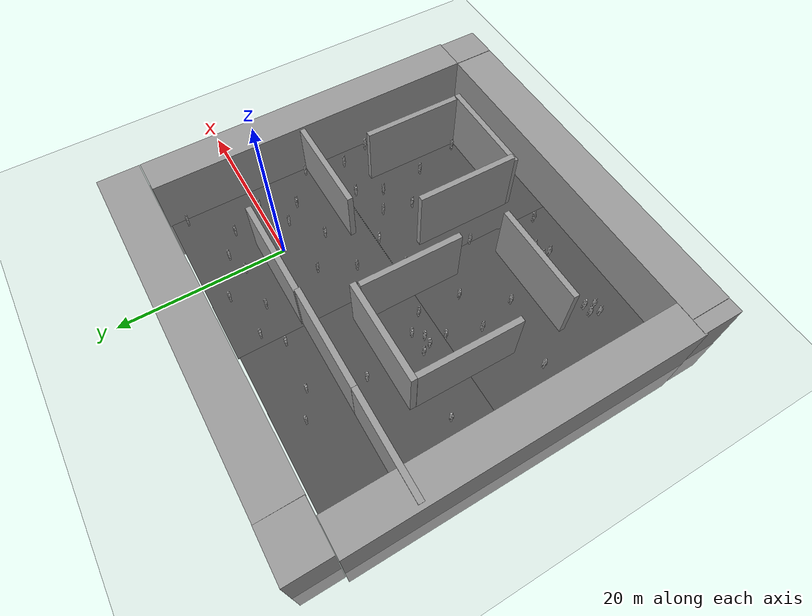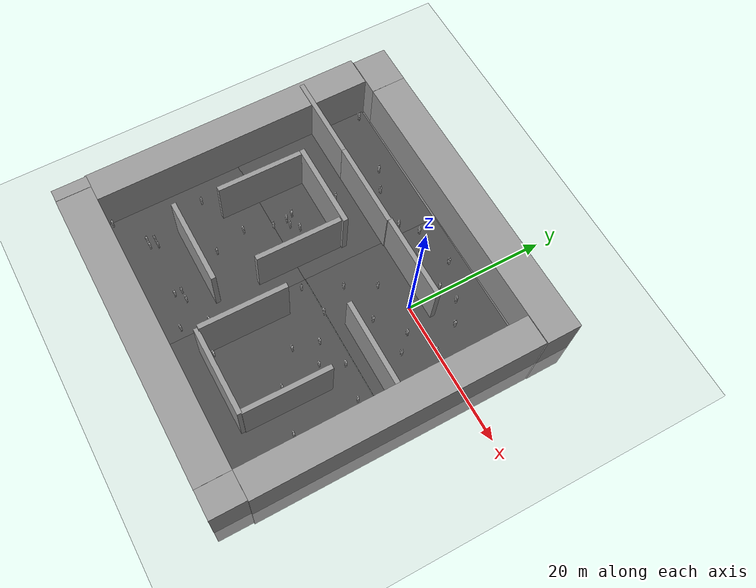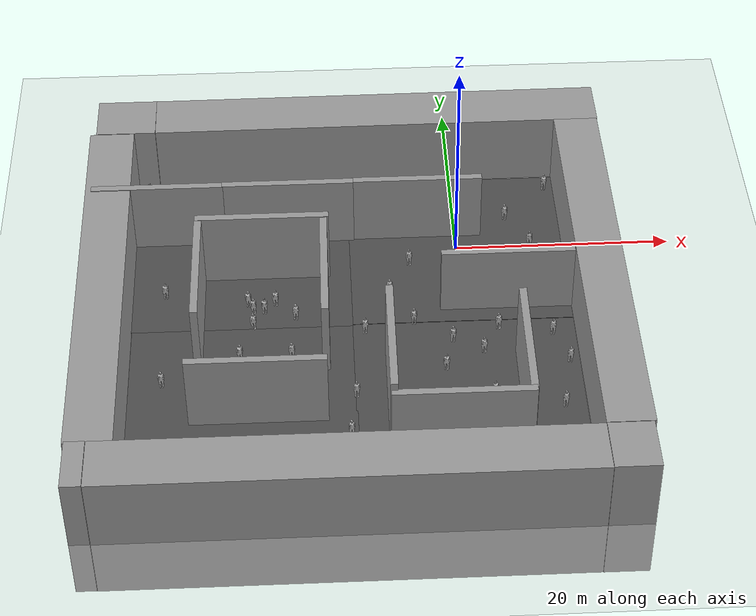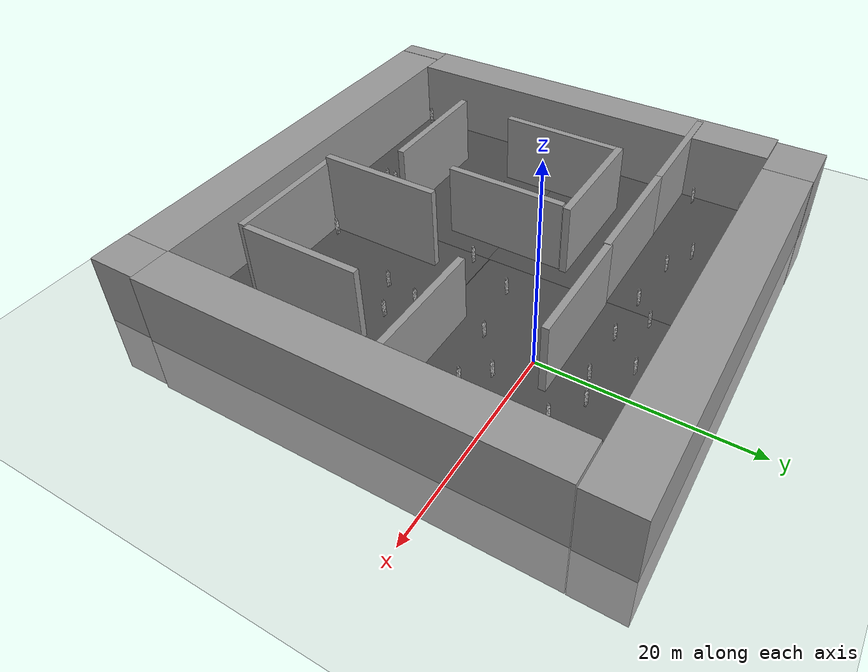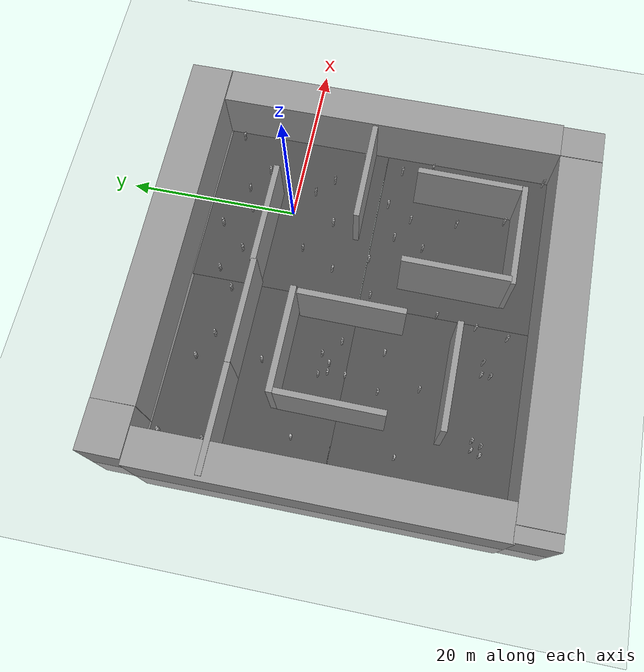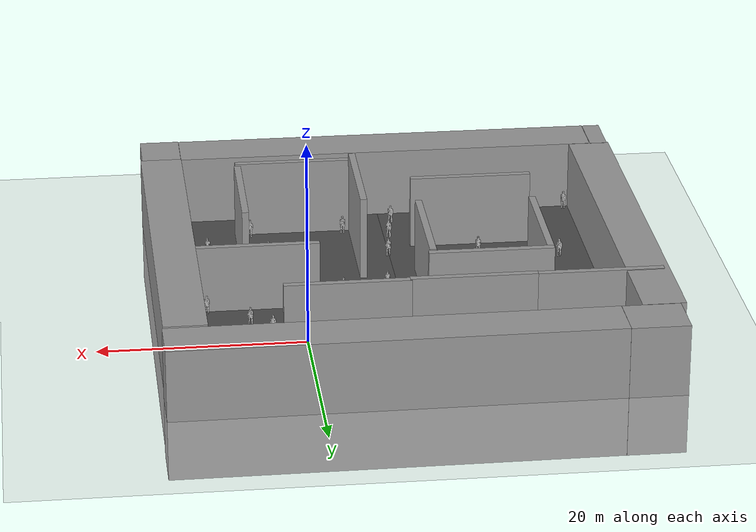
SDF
<sdf version="1.7">
 <world name="default">
  <plugin name="ros_interface_plugin" filename="librotors_gazebo_ros_interface_plugin.so"/>
  <light name="sun" type="directional">
   <pose>0 0 10 0 -0 0</pose>
   <diffuse>0.8 0.8 0.8 1</diffuse>
   <specular>0.1 0.1 0.1 1</specular>
   <attenuation>
    <range>1000</range>
    <constant>0.9</constant>
    <linear>0.01</linear>
    <quadratic>0.001</quadratic>
   </attenuation>
   <direction>-0.5 0.5 -1</direction>
   <spot><inner_angle>0</inner_angle><outer_angle>0</outer_angle><falloff>0</falloff></spot>
  </light>
  <model name="ground_plane">
   <static>1</static>
   <link name="link">
    <collision name="collision">
     <geometry><plane><normal>0 0 1</normal><size>100 100</size></plane></geometry>
     <surface><friction><ode><mu>100</mu><mu2>50</mu2></ode></friction></surface>
    </collision>
    <visual name="visual">
     <cast_shadows>0</cast_shadows>
     <geometry><plane><normal>0 0 1</normal><size>100 100</size></plane></geometry>
     <material>
      <script><uri>file://media/materials/scripts/gazebo.material</uri><name>Gazebo/Grey</name></script>
     </material>
    </visual>
   </link>
  </model>
  <physics type="ode">
   <ode>
    <solver>
     <type>quick</type>
     <iters>50</iters>
     <sor>1.3</sor>
     <use_dynamic_moi_rescaling>0</use_dynamic_moi_rescaling>
    </solver>
    <constraints>
     <cfm>0</cfm>
     <erp>0.2</erp>
     <contact_max_correcting_vel>100</contact_max_correcting_vel>
     <contact_surface_layer>0.001</contact_surface_layer>
    </constraints>
   </ode>
   <max_step_size>0.01</max_step_size>
   <real_time_factor>1</real_time_factor>
   <real_time_update_rate>100</real_time_update_rate>
   <gravity>0 0 -9.8</gravity>
  </physics>
  <atmosphere type="adiabatic"/>
  <scene><ambient>0.4 0.4 0.4 1</ambient><background>0.7 0.7 0.7 1</background><shadows>1</shadows></scene>
  <spherical_coordinates>
   <surface_model>EARTH_WGS84</surface_model>
   <latitude_deg>0</latitude_deg>
   <longitude_deg>0</longitude_deg>
   <elevation>0</elevation>
   <heading_deg>0</heading_deg>
  </spherical_coordinates>
  <gravity>0 0 -9.8</gravity>
  <magnetic_field>6e-06 2.3e-05 -4.2e-05</magnetic_field>
  <model name="pillow">
   <link name="link">
    <visual name="visual">
     <cast_shadows>0</cast_shadows>
     <geometry><box><size>20 20 0.1</size></box></geometry>
     <material>
      <script>
       <uri>model://asphalt_plane/materials/scripts</uri>
       <uri>model://asphalt_plane/materials/textures</uri>
       <name>vrc/asphalt</name>
      </script>
      <ambient>0.5 0.5 0.5 1</ambient>
      <diffuse>0.5 0.5 0.5 1</diffuse>
      <specular>0.2 0.2 0.2 1</specular>
      <emissive>0 0 0 1</emissive>
     </material>
    </visual>
    <collision name="collision">
     <geometry><box><size>20 20 0.1</size></box></geometry>
     <surface>
      <friction>
       <ode><mu>1</mu><mu2>1</mu2><fdir1>0 0 0</fdir1><slip1>0</slip1><slip2>0</slip2></ode>
       <torsional>
        <coefficient>1</coefficient>
        <patch_radius>0</patch_radius>
        <surface_radius>0</surface_radius>
        <use_patch_radius>1</use_patch_radius>
        <ode><slip>0</slip></ode>
       </torsional>
      </friction>
      <bounce><restitution_coefficient>0</restitution_coefficient><threshold>1e+06</threshold></bounce>
      <contact>
       <collide_without_contact>0</collide_without_contact>
       <collide_without_contact_bitmask>1</collide_without_contact_bitmask>
       <collide_bitmask>1</collide_bitmask>
       <ode>
        <soft_cfm>0</soft_cfm>
        <soft_erp>0.2</soft_erp>
        <kp>1e+13</kp>
        <kd>1</kd>
        <max_vel>0.01</max_vel>
        <min_depth>0</min_depth>
       </ode>
       <bullet>
        <split_impulse>1</split_impulse>
        <split_impulse_penetration_threshold>-0.01</split_impulse_penetration_threshold>
        <soft_cfm>0</soft_cfm>
        <soft_erp>0.2</soft_erp>
        <kp>1e+13</kp>
        <kd>1</kd>
       </bullet>
      </contact>
     </surface>
    </collision>
   </link>
   <link name="link_0">
    <pose>-3.5958 2.04635 0.5 0 -0 0</pose>
    <inertial>
     <mass>104.933</mass>
     <inertia><ixx>1481.69</ixx><ixy>0</ixy><ixz>0</ixz><iyy>2754.45</iyy><iyz>0</iyz><izz>1280.56</izz></inertia>
    </inertial>
    <visual name="visual">
     <geometry><box><size>12.0829 0.668042 12.9999</size></box></geometry>
     <material>
      <lighting>1</lighting>
      <script><uri>file://media/materials/scripts/gazebo.material</uri><name>Gazebo/Grey</name></script>
      <ambient>0.3 0.3 0.3 1</ambient>
      <diffuse>0.7 0.7 0.7 1</diffuse>
      <specular>0.01 0.01 0.01 1</specular>
      <emissive>0 0 0 1</emissive>
     </material>
    </visual>
    <collision name="collision">
     <geometry><box><size>12.0829 0.668042 12.9999</size></box></geometry>
     <surface>
      <friction>
       <ode><mu>1</mu><mu2>1</mu2><fdir1>0 0 0</fdir1><slip1>0</slip1><slip2>0</slip2></ode>
       <torsional>
        <coefficient>1</coefficient>
        <patch_radius>0</patch_radius>
        <surface_radius>0</surface_radius>
        <use_patch_radius>1</use_patch_radius>
        <ode><slip>0</slip></ode>
       </torsional>
      </friction>
      <bounce><restitution_coefficient>0</restitution_coefficient><threshold>1e+06</threshold></bounce>
      <contact>
       <collide_without_contact>0</collide_without_contact>
       <collide_without_contact_bitmask>1</collide_without_contact_bitmask>
       <collide_bitmask>1</collide_bitmask>
       <ode>
        <soft_cfm>0</soft_cfm>
        <soft_erp>0.2</soft_erp>
        <kp>1e+13</kp>
        <kd>1</kd>
        <max_vel>0.01</max_vel>
        <min_depth>0</min_depth>
       </ode>
       <bullet>
        <split_impulse>1</split_impulse>
        <split_impulse_penetration_threshold>-0.01</split_impulse_penetration_threshold>
        <soft_cfm>0</soft_cfm>
        <soft_erp>0.2</soft_erp>
        <kp>1e+13</kp>
        <kd>1</kd>
       </bullet>
      </contact>
     </surface>
    </collision>
   </link>
   <link name="link_0_clone">
    <pose>-17.9053 -3.11934 0.5 0 -0 0</pose>
    <inertial>
     <mass>118.443</mass>
     <inertia><ixx>1866.46</ixx><ixy>0</ixy><ixz>0</ixz><iyy>3302.46</iyy><iyz>0</iyz><izz>1446.06</izz></inertia>
    </inertial>
    <visual name="visual">
     <geometry><box><size>12.0829 0.713863 13.7328</size></box></geometry>
     <material>
      <lighting>1</lighting>
      <script><uri>file://media/materials/scripts/gazebo.material</uri><name>Gazebo/Grey</name></script>
      <ambient>0.3 0.3 0.3 1</ambient>
      <diffuse>0.7 0.7 0.7 1</diffuse>
      <specular>0.01 0.01 0.01 1</specular>
      <emissive>0 0 0 1</emissive>
      <shader type="pixel"/>
     </material>
    </visual>
    <collision name="collision">
     <geometry><box><size>12.0829 0.713863 13.7328</size></box></geometry>
     <surface>
      <friction>
       <ode><mu>1</mu><mu2>1</mu2><fdir1>0 0 0</fdir1><slip1>0</slip1><slip2>0</slip2></ode>
       <torsional>
        <coefficient>1</coefficient>
        <patch_radius>0</patch_radius>
        <surface_radius>0</surface_radius>
        <use_patch_radius>1</use_patch_radius>
        <ode><slip>0</slip></ode>
       </torsional>
      </friction>
      <bounce><restitution_coefficient>0</restitution_coefficient><threshold>1e+06</threshold></bounce>
      <contact>
       <collide_without_contact>0</collide_without_contact>
       <collide_without_contact_bitmask>1</collide_without_contact_bitmask>
       <collide_bitmask>1</collide_bitmask>
       <ode>
        <soft_cfm>0</soft_cfm>
        <soft_erp>0.2</soft_erp>
        <kp>1e+13</kp>
        <kd>1</kd>
        <max_vel>0.01</max_vel>
        <min_depth>0</min_depth>
       </ode>
       <bullet>
        <split_impulse>1</split_impulse>
        <split_impulse_penetration_threshold>-0.01</split_impulse_penetration_threshold>
        <soft_cfm>0</soft_cfm>
        <soft_erp>0.2</soft_erp>
        <kp>1e+13</kp>
        <kd>1</kd>
       </bullet>
      </contact>
     </surface>
    </collision>
   </link>
   <link name="link_0_clone_0">
    <pose>-6.91392 12.6282 0.5 0 -0 0.0064</pose>
    <inertial>
     <mass>2670.05</mass>
     <inertia><ixx>42334.8</ixx><ixy>0</ixy><ixz>0</ixz><iyy>432222</iyy><iyz>0</iyz><izz>400641</izz></inertia>
    </inertial>
    <visual name="visual">
     <geometry><box><size>42.1476 4.91564 12.8876</size></box></geometry>
     <material>
      <lighting>1</lighting>
      <script><uri>file://media/materials/scripts/gazebo.material</uri><name>Gazebo/Grey</name></script>
      <ambient>0.3 0.3 0.3 1</ambient>
      <diffuse>0.7 0.7 0.7 1</diffuse>
      <specular>0.01 0.01 0.01 1</specular>
      <emissive>0 0 0 1</emissive>
      <shader type="pixel"/>
     </material>
    </visual>
    <collision name="collision">
     <geometry><box><size>42.1476 4.91564 12.8876</size></box></geometry>
     <surface>
      <friction>
       <ode><mu>1</mu><mu2>1</mu2><fdir1>0 0 0</fdir1><slip1>0</slip1><slip2>0</slip2></ode>
       <torsional>
        <coefficient>1</coefficient>
        <patch_radius>0</patch_radius>
        <surface_radius>0</surface_radius>
        <use_patch_radius>1</use_patch_radius>
        <ode><slip>0</slip></ode>
       </torsional>
      </friction>
      <bounce><restitution_coefficient>0</restitution_coefficient><threshold>1e+06</threshold></bounce>
      <contact>
       <collide_without_contact>0</collide_without_contact>
       <collide_without_contact_bitmask>1</collide_without_contact_bitmask>
       <collide_bitmask>1</collide_bitmask>
       <ode>
        <soft_cfm>0</soft_cfm>
        <soft_erp>0.2</soft_erp>
        <kp>1e+13</kp>
        <kd>1</kd>
        <max_vel>0.01</max_vel>
        <min_depth>0</min_depth>
       </ode>
       <bullet>
        <split_impulse>1</split_impulse>
        <split_impulse_penetration_threshold>-0.01</split_impulse_penetration_threshold>
        <soft_cfm>0</soft_cfm>
        <soft_erp>0.2</soft_erp>
        <kp>1e+13</kp>
        <kd>1</kd>
       </bullet>
      </contact>
     </surface>
    </collision>
   </link>
   <link name="link_0_clone_0_clone_0">
    <pose>4.09467 -8.11934 0.5 0 -0 0</pose>
    <inertial>
     <mass>100.418</mass>
     <inertia><ixx>1298.85</ixx><ixy>0</ixy><ixz>0</ixz><iyy>2516.84</iyy><iyz>0</iyz><izz>1225.46</izz></inertia>
    </inertial>
    <visual name="visual">
     <geometry><box><size>12.0829 0.668042 12.4405</size></box></geometry>
     <material>
      <lighting>1</lighting>
      <script><uri>file://media/materials/scripts/gazebo.material</uri><name>Gazebo/Grey</name></script>
      <ambient>0.3 0.3 0.3 1</ambient>
      <diffuse>0.7 0.7 0.7 1</diffuse>
      <specular>0.01 0.01 0.01 1</specular>
      <emissive>0 0 0 1</emissive>
      <shader type="pixel"/>
     </material>
    </visual>
    <collision name="collision">
     <geometry><box><size>12.0829 0.668042 12.4405</size></box></geometry>
     <surface>
      <friction>
       <ode><mu>1</mu><mu2>1</mu2><fdir1>0 0 0</fdir1><slip1>0</slip1><slip2>0</slip2></ode>
       <torsional>
        <coefficient>1</coefficient>
        <patch_radius>0</patch_radius>
        <surface_radius>0</surface_radius>
        <use_patch_radius>1</use_patch_radius>
        <ode><slip>0</slip></ode>
       </torsional>
      </friction>
      <bounce><restitution_coefficient>0</restitution_coefficient><threshold>1e+06</threshold></bounce>
      <contact>
       <collide_without_contact>0</collide_without_contact>
       <collide_without_contact_bitmask>1</collide_without_contact_bitmask>
       <collide_bitmask>1</collide_bitmask>
       <ode>
        <soft_cfm>0</soft_cfm>
        <soft_erp>0.2</soft_erp>
        <kp>1e+13</kp>
        <kd>1</kd>
        <max_vel>0.01</max_vel>
        <min_depth>0</min_depth>
       </ode>
       <bullet>
        <split_impulse>1</split_impulse>
        <split_impulse_penetration_threshold>-0.01</split_impulse_penetration_threshold>
        <soft_cfm>0</soft_cfm>
        <soft_erp>0.2</soft_erp>
        <kp>1e+13</kp>
        <kd>1</kd>
       </bullet>
      </contact>
     </surface>
    </collision>
   </link>
   <link name="link_0_clone_0_clone_1">
    <pose>-18.4124 -21.5717 0.5 0 -0 0</pose>
    <inertial>
     <mass>111.127</mass>
     <inertia><ixx>1759.36</ixx><ixy>0</ixy><ixz>0</ixz><iyy>3107.24</iyy><iyz>0</iyz><izz>1356.15</izz></inertia>
    </inertial>
    <visual name="visual">
     <geometry><box><size>12.0829 0.668042 13.7672</size></box></geometry>
     <material>
      <lighting>1</lighting>
      <script><uri>file://media/materials/scripts/gazebo.material</uri><name>Gazebo/Grey</name></script>
      <ambient>0.3 0.3 0.3 1</ambient>
      <diffuse>0.7 0.7 0.7 1</diffuse>
      <specular>0.01 0.01 0.01 1</specular>
      <emissive>0 0 0 1</emissive>
      <shader type="pixel"/>
     </material>
    </visual>
    <collision name="collision">
     <geometry><box><size>12.0829 0.668042 13.7672</size></box></geometry>
     <surface>
      <friction>
       <ode><mu>1</mu><mu2>1</mu2><fdir1>0 0 0</fdir1><slip1>0</slip1><slip2>0</slip2></ode>
       <torsional>
        <coefficient>1</coefficient>
        <patch_radius>0</patch_radius>
        <surface_radius>0</surface_radius>
        <use_patch_radius>1</use_patch_radius>
        <ode><slip>0</slip></ode>
       </torsional>
      </friction>
      <bounce><restitution_coefficient>0</restitution_coefficient><threshold>1e+06</threshold></bounce>
      <contact>
       <collide_without_contact>0</collide_without_contact>
       <collide_without_contact_bitmask>1</collide_without_contact_bitmask>
       <collide_bitmask>1</collide_bitmask>
       <ode>
        <soft_cfm>0</soft_cfm>
        <soft_erp>0.2</soft_erp>
        <kp>1e+13</kp>
        <kd>1</kd>
        <max_vel>0.01</max_vel>
        <min_depth>0</min_depth>
       </ode>
       <bullet>
        <split_impulse>1</split_impulse>
        <split_impulse_penetration_threshold>-0.01</split_impulse_penetration_threshold>
        <soft_cfm>0</soft_cfm>
        <soft_erp>0.2</soft_erp>
        <kp>1e+13</kp>
        <kd>1</kd>
       </bullet>
      </contact>
     </surface>
    </collision>
   </link>
   <link name="link_0_clone_0_clone_2">
    <pose>-1.17788 -26.3842 0.5 0 -0 0</pose>
    <inertial>
     <mass>117.056</mass>
     <inertia><ixx>2055.8</ixx><ixy>0</ixy><ixz>0</ixz><iyy>3475.6</iyy><iyz>0</iyz><izz>1428.51</izz></inertia>
    </inertial>
    <visual name="visual">
     <geometry><box><size>12.0829 0.668042 14.5018</size></box></geometry>
     <material>
      <lighting>1</lighting>
      <script><uri>file://media/materials/scripts/gazebo.material</uri><name>Gazebo/Grey</name></script>
      <ambient>0.3 0.3 0.3 1</ambient>
      <diffuse>0.7 0.7 0.7 1</diffuse>
      <specular>0.01 0.01 0.01 1</specular>
      <emissive>0 0 0 1</emissive>
      <shader type="pixel"/>
     </material>
    </visual>
    <collision name="collision">
     <geometry><box><size>12.0829 0.668042 14.5018</size></box></geometry>
     <surface>
      <friction>
       <ode><mu>1</mu><mu2>1</mu2><fdir1>0 0 0</fdir1><slip1>0</slip1><slip2>0</slip2></ode>
       <torsional>
        <coefficient>1</coefficient>
        <patch_radius>0</patch_radius>
        <surface_radius>0</surface_radius>
        <use_patch_radius>1</use_patch_radius>
        <ode><slip>0</slip></ode>
       </torsional>
      </friction>
      <bounce><restitution_coefficient>0</restitution_coefficient><threshold>1e+06</threshold></bounce>
      <contact>
       <collide_without_contact>0</collide_without_contact>
       <collide_without_contact_bitmask>1</collide_without_contact_bitmask>
       <collide_bitmask>1</collide_bitmask>
       <ode>
        <soft_cfm>0</soft_cfm>
        <soft_erp>0.2</soft_erp>
        <kp>1e+13</kp>
        <kd>1</kd>
        <max_vel>0.01</max_vel>
        <min_depth>0</min_depth>
       </ode>
       <bullet>
        <split_impulse>1</split_impulse>
        <split_impulse_penetration_threshold>-0.01</split_impulse_penetration_threshold>
        <soft_cfm>0</soft_cfm>
        <soft_erp>0.2</soft_erp>
        <kp>1e+13</kp>
        <kd>1</kd>
       </bullet>
      </contact>
     </surface>
    </collision>
   </link>
   <link name="link_0_clone_0_clone_3">
    <pose>-30.7681 12.5167 0.5 0 -0 0</pose>
    <inertial>
     <mass>350.589</mass>
     <inertia><ixx>5546.34</ixx><ixy>0</ixy><ixz>0</ixz><iyy>5737.39</iyy><iyz>0</iyz><izz>1603.12</izz></inertia>
    </inertial>
    <visual name="visual">
     <geometry><box><size>5.54125 4.91564 12.8711</size></box></geometry>
     <material>
      <lighting>1</lighting>
      <script><uri>file://media/materials/scripts/gazebo.material</uri><name>Gazebo/Grey</name></script>
      <ambient>0.3 0.3 0.3 1</ambient>
      <diffuse>0.7 0.7 0.7 1</diffuse>
      <specular>0.01 0.01 0.01 1</specular>
      <emissive>0 0 0 1</emissive>
      <shader type="pixel"/>
     </material>
    </visual>
    <collision name="collision">
     <geometry><box><size>5.54125 4.91564 12.8711</size></box></geometry>
     <surface>
      <friction>
       <ode><mu>1</mu><mu2>1</mu2><fdir1>0 0 0</fdir1><slip1>0</slip1><slip2>0</slip2></ode>
       <torsional>
        <coefficient>1</coefficient>
        <patch_radius>0</patch_radius>
        <surface_radius>0</surface_radius>
        <use_patch_radius>1</use_patch_radius>
        <ode><slip>0</slip></ode>
       </torsional>
      </friction>
      <bounce><restitution_coefficient>0</restitution_coefficient><threshold>1e+06</threshold></bounce>
      <contact>
       <collide_without_contact>0</collide_without_contact>
       <collide_without_contact_bitmask>1</collide_without_contact_bitmask>
       <collide_bitmask>1</collide_bitmask>
       <ode>
        <soft_cfm>0</soft_cfm>
        <soft_erp>0.2</soft_erp>
        <kp>1e+13</kp>
        <kd>1</kd>
        <max_vel>0.01</max_vel>
        <min_depth>0</min_depth>
       </ode>
       <bullet>
        <split_impulse>1</split_impulse>
        <split_impulse_penetration_threshold>-0.01</split_impulse_penetration_threshold>
        <soft_cfm>0</soft_cfm>
        <soft_erp>0.2</soft_erp>
        <kp>1e+13</kp>
        <kd>1</kd>
       </bullet>
      </contact>
     </surface>
    </collision>
   </link>
   <link name="link_0_clone_0_clone_3_clone">
    <pose>-32.9522 -32.3454 0.5 0 -0 0</pose>
    <inertial>
     <mass>110.757</mass>
     <inertia><ixx>1757.01</ixx><ixy>0</ixy><ixz>0</ixz><iyy>1562.16</iyy><iyz>0</iyz><izz>251.243</izz></inertia>
    </inertial>
    <visual name="visual">
     <geometry><box><size>1.74782 4.91564 12.8914</size></box></geometry>
     <material>
      <lighting>1</lighting>
      <script><uri>file://media/materials/scripts/gazebo.material</uri><name>Gazebo/Grey</name></script>
      <ambient>0.3 0.3 0.3 1</ambient>
      <diffuse>0.7 0.7 0.7 1</diffuse>
      <specular>0.01 0.01 0.01 1</specular>
      <emissive>0 0 0 1</emissive>
      <shader type="pixel"/>
     </material>
    </visual>
    <collision name="collision">
     <geometry><box><size>1.74782 4.91564 12.8914</size></box></geometry>
     <surface>
      <friction>
       <ode><mu>1</mu><mu2>1</mu2><fdir1>0 0 0</fdir1><slip1>0</slip1><slip2>0</slip2></ode>
       <torsional>
        <coefficient>1</coefficient>
        <patch_radius>0</patch_radius>
        <surface_radius>0</surface_radius>
        <use_patch_radius>1</use_patch_radius>
        <ode><slip>0</slip></ode>
       </torsional>
      </friction>
      <bounce><restitution_coefficient>0</restitution_coefficient><threshold>1e+06</threshold></bounce>
      <contact>
       <collide_without_contact>0</collide_without_contact>
       <collide_without_contact_bitmask>1</collide_without_contact_bitmask>
       <collide_bitmask>1</collide_bitmask>
       <ode>
        <soft_cfm>0</soft_cfm>
        <soft_erp>0.2</soft_erp>
        <kp>1e+13</kp>
        <kd>1</kd>
        <max_vel>0.01</max_vel>
        <min_depth>0</min_depth>
       </ode>
       <bullet>
        <split_impulse>1</split_impulse>
        <split_impulse_penetration_threshold>-0.01</split_impulse_penetration_threshold>
        <soft_cfm>0</soft_cfm>
        <soft_erp>0.2</soft_erp>
        <kp>1e+13</kp>
        <kd>1</kd>
       </bullet>
      </contact>
     </surface>
    </collision>
   </link>
   <link name="link_0_clone_0_clone_3_clone_clone">
    <pose>12.0862 -32.3668 0.5 0 -0 0</pose>
    <inertial>
     <mass>249.83</mass>
     <inertia><ixx>4011.02</ixx><ixy>0</ixy><ixz>0</ixz><iyy>3827.09</iyy><iyz>0</iyz><izz>822.306</izz></inertia>
    </inertial>
    <visual name="visual">
     <geometry><box><size>3.91552 4.91564 12.9802</size></box></geometry>
     <material>
      <lighting>1</lighting>
      <script><uri>file://media/materials/scripts/gazebo.material</uri><name>Gazebo/Grey</name></script>
      <ambient>0.3 0.3 0.3 1</ambient>
      <diffuse>0.7 0.7 0.7 1</diffuse>
      <specular>0.01 0.01 0.01 1</specular>
      <emissive>0 0 0 1</emissive>
      <shader type="pixel"/>
     </material>
    </visual>
    <collision name="collision">
     <geometry><box><size>3.91552 4.91564 12.9802</size></box></geometry>
     <surface>
      <friction>
       <ode><mu>1</mu><mu2>1</mu2><fdir1>0 0 0</fdir1><slip1>0</slip1><slip2>0</slip2></ode>
       <torsional>
        <coefficient>1</coefficient>
        <patch_radius>0</patch_radius>
        <surface_radius>0</surface_radius>
        <use_patch_radius>1</use_patch_radius>
        <ode><slip>0</slip></ode>
       </torsional>
      </friction>
      <bounce><restitution_coefficient>0</restitution_coefficient><threshold>1e+06</threshold></bounce>
      <contact>
       <collide_without_contact>0</collide_without_contact>
       <collide_without_contact_bitmask>1</collide_without_contact_bitmask>
       <collide_bitmask>1</collide_bitmask>
       <ode>
        <soft_cfm>0</soft_cfm>
        <soft_erp>0.2</soft_erp>
        <kp>1e+13</kp>
        <kd>1</kd>
        <max_vel>0.01</max_vel>
        <min_depth>0</min_depth>
       </ode>
       <bullet>
        <split_impulse>1</split_impulse>
        <split_impulse_penetration_threshold>-0.01</split_impulse_penetration_threshold>
        <soft_cfm>0</soft_cfm>
        <soft_erp>0.2</soft_erp>
        <kp>1e+13</kp>
        <kd>1</kd>
       </bullet>
      </contact>
     </surface>
    </collision>
   </link>
   <link name="link_0_clone_0_clone_4">
    <pose>-10.9678 -32.384 0.5 0 -0 0</pose>
    <inertial>
     <mass>2672.62</mass>
     <inertia><ixx>42446.8</ixx><ixy>0</ixy><ixz>0</ixz><iyy>432709</iyy><iyz>0</iyz><izz>401026</izz></inertia>
    </inertial>
    <visual name="visual">
     <geometry><box><size>42.1476 4.91564 12.9</size></box></geometry>
     <material>
      <lighting>1</lighting>
      <script><uri>file://media/materials/scripts/gazebo.material</uri><name>Gazebo/Grey</name></script>
      <ambient>0.3 0.3 0.3 1</ambient>
      <diffuse>0.7 0.7 0.7 1</diffuse>
      <specular>0.01 0.01 0.01 1</specular>
      <emissive>0 0 0 1</emissive>
      <shader type="pixel"/>
     </material>
    </visual>
    <collision name="collision">
     <geometry><box><size>42.1476 4.91564 12.9</size></box></geometry>
     <surface>
      <friction>
       <ode><mu>1</mu><mu2>1</mu2><fdir1>0 0 0</fdir1><slip1>0</slip1><slip2>0</slip2></ode>
       <torsional>
        <coefficient>1</coefficient>
        <patch_radius>0</patch_radius>
        <surface_radius>0</surface_radius>
        <use_patch_radius>1</use_patch_radius>
        <ode><slip>0</slip></ode>
       </torsional>
      </friction>
      <bounce><restitution_coefficient>0</restitution_coefficient><threshold>1e+06</threshold></bounce>
      <contact>
       <collide_without_contact>0</collide_without_contact>
       <collide_without_contact_bitmask>1</collide_without_contact_bitmask>
       <collide_bitmask>1</collide_bitmask>
       <ode>
        <soft_cfm>0</soft_cfm>
        <soft_erp>0.2</soft_erp>
        <kp>1e+13</kp>
        <kd>1</kd>
        <max_vel>0.01</max_vel>
        <min_depth>0</min_depth>
       </ode>
       <bullet>
        <split_impulse>1</split_impulse>
        <split_impulse_penetration_threshold>-0.01</split_impulse_penetration_threshold>
        <soft_cfm>0</soft_cfm>
        <soft_erp>0.2</soft_erp>
        <kp>1e+13</kp>
        <kd>1</kd>
       </bullet>
      </contact>
     </surface>
    </collision>
   </link>
   <link name="link_0_clone_0_clone_clone">
    <pose>12.0974 -9.86857 0.5 0 0 -1.56777</pose>
    <inertial>
     <mass>2161.3</mass>
     <inertia><ixx>33855.1</ixx><ixy>0</ixy><ixz>0</ixz><iyy>320569</iyy><iyz>0</iyz><izz>292832</izz></inertia>
    </inertial>
    <visual name="visual">
     <geometry><box><size>40.1108 4.1207 13.0764</size></box></geometry>
     <material>
      <lighting>1</lighting>
      <script><uri>file://media/materials/scripts/gazebo.material</uri><name>Gazebo/Grey</name></script>
      <ambient>0.3 0.3 0.3 1</ambient>
      <diffuse>0.7 0.7 0.7 1</diffuse>
      <specular>0.01 0.01 0.01 1</specular>
      <emissive>0 0 0 1</emissive>
      <shader type="pixel"/>
     </material>
    </visual>
    <collision name="collision">
     <geometry><box><size>40.1108 4.1207 13.0764</size></box></geometry>
     <surface>
      <friction>
       <ode><mu>1</mu><mu2>1</mu2><fdir1>0 0 0</fdir1><slip1>0</slip1><slip2>0</slip2></ode>
       <torsional>
        <coefficient>1</coefficient>
        <patch_radius>0</patch_radius>
        <surface_radius>0</surface_radius>
        <use_patch_radius>1</use_patch_radius>
        <ode><slip>0</slip></ode>
       </torsional>
      </friction>
      <bounce><restitution_coefficient>0</restitution_coefficient><threshold>1e+06</threshold></bounce>
      <contact>
       <collide_without_contact>0</collide_without_contact>
       <collide_without_contact_bitmask>1</collide_without_contact_bitmask>
       <collide_bitmask>1</collide_bitmask>
       <ode>
        <soft_cfm>0</soft_cfm>
        <soft_erp>0.2</soft_erp>
        <kp>1e+13</kp>
        <kd>1</kd>
        <max_vel>0.01</max_vel>
        <min_depth>0</min_depth>
       </ode>
       <bullet>
        <split_impulse>1</split_impulse>
        <split_impulse_penetration_threshold>-0.01</split_impulse_penetration_threshold>
        <soft_cfm>0</soft_cfm>
        <soft_erp>0.2</soft_erp>
        <kp>1e+13</kp>
        <kd>1</kd>
       </bullet>
      </contact>
     </surface>
    </collision>
   </link>
   <link name="link_0_clone_0_clone_clone_clone">
    <pose>-31.9703 -10.059 0.5 0 0 -1.56777</pose>
    <inertial>
     <mass>2126.69</mass>
     <inertia><ixx>32350.5</ixx><ixy>0</ixy><ixz>0</ixz><iyy>314474</iyy><iyz>0</iyz><izz>288144</izz></inertia>
    </inertial>
    <visual name="visual">
     <geometry><box><size>40.1108 4.1207 12.867</size></box></geometry>
     <material>
      <lighting>1</lighting>
      <script><uri>file://media/materials/scripts/gazebo.material</uri><name>Gazebo/Grey</name></script>
      <ambient>0.3 0.3 0.3 1</ambient>
      <diffuse>0.7 0.7 0.7 1</diffuse>
      <specular>0.01 0.01 0.01 1</specular>
      <emissive>0 0 0 1</emissive>
      <shader type="pixel"/>
     </material>
    </visual>
    <collision name="collision">
     <geometry><box><size>40.1108 4.1207 12.867</size></box></geometry>
     <surface>
      <friction>
       <ode><mu>1</mu><mu2>1</mu2><fdir1>0 0 0</fdir1><slip1>0</slip1><slip2>0</slip2></ode>
       <torsional>
        <coefficient>1</coefficient>
        <patch_radius>0</patch_radius>
        <surface_radius>0</surface_radius>
        <use_patch_radius>1</use_patch_radius>
        <ode><slip>0</slip></ode>
       </torsional>
      </friction>
      <bounce><restitution_coefficient>0</restitution_coefficient><threshold>1e+06</threshold></bounce>
      <contact>
       <collide_without_contact>0</collide_without_contact>
       <collide_without_contact_bitmask>1</collide_without_contact_bitmask>
       <collide_bitmask>1</collide_bitmask>
       <ode>
        <soft_cfm>0</soft_cfm>
        <soft_erp>0.2</soft_erp>
        <kp>1e+13</kp>
        <kd>1</kd>
        <max_vel>0.01</max_vel>
        <min_depth>0</min_depth>
       </ode>
       <bullet>
        <split_impulse>1</split_impulse>
        <split_impulse_penetration_threshold>-0.01</split_impulse_penetration_threshold>
        <soft_cfm>0</soft_cfm>
        <soft_erp>0.2</soft_erp>
        <kp>1e+13</kp>
        <kd>1</kd>
       </bullet>
      </contact>
     </surface>
    </collision>
   </link>
   <link name="link_0_clone_1">
    <pose>-23.6918 -9.52482 0.5 0 0 -1.5784</pose>
    <inertial>
     <mass>110.395</mass>
     <inertia><ixx>1724.88</ixx><ixy>0</ixy><ixz>0</ixz><iyy>3063.88</iyy><iyz>0</iyz><izz>1347.22</izz></inertia>
    </inertial>
    <visual name="visual">
     <geometry><box><size>12.0829 0.668042 13.6765</size></box></geometry>
     <material>
      <lighting>1</lighting>
      <script><uri>file://media/materials/scripts/gazebo.material</uri><name>Gazebo/Grey</name></script>
      <ambient>0.3 0.3 0.3 1</ambient>
      <diffuse>0.7 0.7 0.7 1</diffuse>
      <specular>0.01 0.01 0.01 1</specular>
      <emissive>0 0 0 1</emissive>
      <shader type="pixel"/>
     </material>
    </visual>
    <collision name="collision">
     <geometry><box><size>12.0829 0.668042 13.6765</size></box></geometry>
     <surface>
      <friction>
       <ode><mu>1</mu><mu2>1</mu2><fdir1>0 0 0</fdir1><slip1>0</slip1><slip2>0</slip2></ode>
       <torsional>
        <coefficient>1</coefficient>
        <patch_radius>0</patch_radius>
        <surface_radius>0</surface_radius>
        <use_patch_radius>1</use_patch_radius>
        <ode><slip>0</slip></ode>
       </torsional>
      </friction>
      <bounce><restitution_coefficient>0</restitution_coefficient><threshold>1e+06</threshold></bounce>
      <contact>
       <collide_without_contact>0</collide_without_contact>
       <collide_without_contact_bitmask>1</collide_without_contact_bitmask>
       <collide_bitmask>1</collide_bitmask>
       <ode>
        <soft_cfm>0</soft_cfm>
        <soft_erp>0.2</soft_erp>
        <kp>1e+13</kp>
        <kd>1</kd>
        <max_vel>0.01</max_vel>
        <min_depth>0</min_depth>
       </ode>
       <bullet>
        <split_impulse>1</split_impulse>
        <split_impulse_penetration_threshold>-0.01</split_impulse_penetration_threshold>
        <soft_cfm>0</soft_cfm>
        <soft_erp>0.2</soft_erp>
        <kp>1e+13</kp>
        <kd>1</kd>
       </bullet>
      </contact>
     </surface>
    </collision>
   </link>
   <link name="link_0_clone_1_clone">
    <pose>-12.4048 -9.66339 0.5 0 0 -1.5784</pose>
    <inertial>
     <mass>111.663</mass>
     <inertia><ixx>1784.93</ixx><ixy>0</ixy><ixz>0</ixz><iyy>3139.32</iyy><iyz>0</iyz><izz>1362.7</izz></inertia>
    </inertial>
    <visual name="visual">
     <geometry><box><size>12.0829 0.668042 13.8337</size></box></geometry>
     <material>
      <lighting>1</lighting>
      <script><uri>file://media/materials/scripts/gazebo.material</uri><name>Gazebo/Grey</name></script>
      <ambient>0.3 0.3 0.3 1</ambient>
      <diffuse>0.7 0.7 0.7 1</diffuse>
      <specular>0.01 0.01 0.01 1</specular>
      <emissive>0 0 0 1</emissive>
      <shader type="pixel"/>
     </material>
    </visual>
    <collision name="collision">
     <geometry><box><size>12.0829 0.668042 13.8337</size></box></geometry>
     <surface>
      <friction>
       <ode><mu>1</mu><mu2>1</mu2><fdir1>0 0 0</fdir1><slip1>0</slip1><slip2>0</slip2></ode>
       <torsional>
        <coefficient>1</coefficient>
        <patch_radius>0</patch_radius>
        <surface_radius>0</surface_radius>
        <use_patch_radius>1</use_patch_radius>
        <ode><slip>0</slip></ode>
       </torsional>
      </friction>
      <bounce><restitution_coefficient>0</restitution_coefficient><threshold>1e+06</threshold></bounce>
      <contact>
       <collide_without_contact>0</collide_without_contact>
       <collide_without_contact_bitmask>1</collide_without_contact_bitmask>
       <collide_bitmask>1</collide_bitmask>
       <ode>
        <soft_cfm>0</soft_cfm>
        <soft_erp>0.2</soft_erp>
        <kp>1e+13</kp>
        <kd>1</kd>
        <max_vel>0.01</max_vel>
        <min_depth>0</min_depth>
       </ode>
       <bullet>
        <split_impulse>1</split_impulse>
        <split_impulse_penetration_threshold>-0.01</split_impulse_penetration_threshold>
        <soft_cfm>0</soft_cfm>
        <soft_erp>0.2</soft_erp>
        <kp>1e+13</kp>
        <kd>1</kd>
       </bullet>
      </contact>
     </surface>
    </collision>
   </link>
   <link name="link_0_clone_1_clone_clone">
    <pose>-6.90533 -20.1193 0.5 0 0 -1.5784</pose>
    <inertial>
     <mass>128.082</mass>
     <inertia><ixx>2692.23</ixx><ixy>0</ixy><ixz>0</ixz><iyy>4245.77</iyy><iyz>0</iyz><izz>1563.06</izz></inertia>
    </inertial>
    <visual name="visual">
     <geometry><box><size>12.0829 0.668042 15.8678</size></box></geometry>
     <material>
      <lighting>1</lighting>
      <script><uri>file://media/materials/scripts/gazebo.material</uri><name>Gazebo/Grey</name></script>
      <ambient>0.3 0.3 0.3 1</ambient>
      <diffuse>0.7 0.7 0.7 1</diffuse>
      <specular>0.01 0.01 0.01 1</specular>
      <emissive>0 0 0 1</emissive>
      <shader type="pixel"/>
     </material>
    </visual>
    <collision name="collision">
     <geometry><box><size>12.0829 0.668042 15.8678</size></box></geometry>
     <surface>
      <friction>
       <ode><mu>1</mu><mu2>1</mu2><fdir1>0 0 0</fdir1><slip1>0</slip1><slip2>0</slip2></ode>
       <torsional>
        <coefficient>1</coefficient>
        <patch_radius>0</patch_radius>
        <surface_radius>0</surface_radius>
        <use_patch_radius>1</use_patch_radius>
        <ode><slip>0</slip></ode>
       </torsional>
      </friction>
      <bounce><restitution_coefficient>0</restitution_coefficient><threshold>1e+06</threshold></bounce>
      <contact>
       <collide_without_contact>0</collide_without_contact>
       <collide_without_contact_bitmask>1</collide_without_contact_bitmask>
       <collide_bitmask>1</collide_bitmask>
       <ode>
        <soft_cfm>0</soft_cfm>
        <soft_erp>0.2</soft_erp>
        <kp>1e+13</kp>
        <kd>1</kd>
        <max_vel>0.01</max_vel>
        <min_depth>0</min_depth>
       </ode>
       <bullet>
        <split_impulse>1</split_impulse>
        <split_impulse_penetration_threshold>-0.01</split_impulse_penetration_threshold>
        <soft_cfm>0</soft_cfm>
        <soft_erp>0.2</soft_erp>
        <kp>1e+13</kp>
        <kd>1</kd>
       </bullet>
      </contact>
     </surface>
    </collision>
   </link>
   <link name="link_0_clone_1_clone_clone_clone">
    <pose>4.68945 -20.1193 0.5 0 0 -1.5784</pose>
    <inertial>
     <mass>114.352</mass>
     <inertia><ixx>1916.77</ixx><ixy>0</ixy><ixz>0</ixz><iyy>3303.77</iyy><iyz>0</iyz><izz>1395.5</izz></inertia>
    </inertial>
    <visual name="visual">
     <geometry><box><size>12.0829 0.668042 14.1667</size></box></geometry>
     <material>
      <lighting>1</lighting>
      <script><uri>file://media/materials/scripts/gazebo.material</uri><name>Gazebo/Grey</name></script>
      <ambient>0.3 0.3 0.3 1</ambient>
      <diffuse>0.7 0.7 0.7 1</diffuse>
      <specular>0.01 0.01 0.01 1</specular>
      <emissive>0 0 0 1</emissive>
      <shader type="pixel"/>
     </material>
    </visual>
    <collision name="collision">
     <geometry><box><size>12.0829 0.668042 14.1667</size></box></geometry>
     <surface>
      <friction>
       <ode><mu>1</mu><mu2>1</mu2><fdir1>0 0 0</fdir1><slip1>0</slip1><slip2>0</slip2></ode>
       <torsional>
        <coefficient>1</coefficient>
        <patch_radius>0</patch_radius>
        <surface_radius>0</surface_radius>
        <use_patch_radius>1</use_patch_radius>
        <ode><slip>0</slip></ode>
       </torsional>
      </friction>
      <bounce><restitution_coefficient>0</restitution_coefficient><threshold>1e+06</threshold></bounce>
      <contact>
       <collide_without_contact>0</collide_without_contact>
       <collide_without_contact_bitmask>1</collide_without_contact_bitmask>
       <collide_bitmask>1</collide_bitmask>
       <ode>
        <soft_cfm>0</soft_cfm>
        <soft_erp>0.2</soft_erp>
        <kp>1e+13</kp>
        <kd>1</kd>
        <max_vel>0.01</max_vel>
        <min_depth>0</min_depth>
       </ode>
       <bullet>
        <split_impulse>1</split_impulse>
        <split_impulse_penetration_threshold>-0.01</split_impulse_penetration_threshold>
        <soft_cfm>0</soft_cfm>
        <soft_erp>0.2</soft_erp>
        <kp>1e+13</kp>
        <kd>1</kd>
       </bullet>
      </contact>
     </surface>
    </collision>
   </link>
   <link name="link_0_clone_2">
    <pose>-15.5128 1.9188 0.5 0 -0 0</pose>
    <inertial>
     <mass>105.543</mass>
     <inertia><ixx>1507.64</ixx><ixy>0</ixy><ixz>0</ixz><iyy>2787.8</iyy><iyz>0</iyz><izz>1288.01</izz></inertia>
    </inertial>
    <visual name="visual">
     <geometry><box><size>12.0829 0.668042 13.0755</size></box></geometry>
     <material>
      <lighting>1</lighting>
      <script><uri>file://media/materials/scripts/gazebo.material</uri><name>Gazebo/Grey</name></script>
      <ambient>0.3 0.3 0.3 1</ambient>
      <diffuse>0.7 0.7 0.7 1</diffuse>
      <specular>0.01 0.01 0.01 1</specular>
      <emissive>0 0 0 1</emissive>
      <shader type="pixel"/>
     </material>
    </visual>
    <collision name="collision">
     <geometry><box><size>12.0829 0.668042 13.0755</size></box></geometry>
     <surface>
      <friction>
       <ode><mu>1</mu><mu2>1</mu2><fdir1>0 0 0</fdir1><slip1>0</slip1><slip2>0</slip2></ode>
       <torsional>
        <coefficient>1</coefficient>
        <patch_radius>0</patch_radius>
        <surface_radius>0</surface_radius>
        <use_patch_radius>1</use_patch_radius>
        <ode><slip>0</slip></ode>
       </torsional>
      </friction>
      <bounce><restitution_coefficient>0</restitution_coefficient><threshold>1e+06</threshold></bounce>
      <contact>
       <collide_without_contact>0</collide_without_contact>
       <collide_without_contact_bitmask>1</collide_without_contact_bitmask>
       <collide_bitmask>1</collide_bitmask>
       <ode>
        <soft_cfm>0</soft_cfm>
        <soft_erp>0.2</soft_erp>
        <kp>1e+13</kp>
        <kd>1</kd>
        <max_vel>0.01</max_vel>
        <min_depth>0</min_depth>
       </ode>
       <bullet>
        <split_impulse>1</split_impulse>
        <split_impulse_penetration_threshold>-0.01</split_impulse_penetration_threshold>
        <soft_cfm>0</soft_cfm>
        <soft_erp>0.2</soft_erp>
        <kp>1e+13</kp>
        <kd>1</kd>
       </bullet>
      </contact>
     </surface>
    </collision>
   </link>
   <link name="link_0_clone_3">
    <pose>-27.5128 1.91417 0.5 0 -0 0</pose>
    <inertial>
     <mass>104.933</mass>
     <inertia><ixx>1481.69</ixx><ixy>0</ixy><ixz>0</ixz><iyy>2754.45</iyy><iyz>0</iyz><izz>1280.56</izz></inertia>
    </inertial>
    <visual name="visual">
     <geometry><box><size>12.0829 0.668042 12.9999</size></box></geometry>
     <material>
      <lighting>1</lighting>
      <script><uri>file://media/materials/scripts/gazebo.material</uri><name>Gazebo/Grey</name></script>
      <ambient>0.3 0.3 0.3 1</ambient>
      <diffuse>0.7 0.7 0.7 1</diffuse>
      <specular>0.01 0.01 0.01 1</specular>
      <emissive>0 0 0 1</emissive>
      <shader type="pixel"/>
     </material>
    </visual>
    <collision name="collision">
     <geometry><box><size>12.0829 0.668042 12.9999</size></box></geometry>
     <surface>
      <friction>
       <ode><mu>1</mu><mu2>1</mu2><fdir1>0 0 0</fdir1><slip1>0</slip1><slip2>0</slip2></ode>
       <torsional>
        <coefficient>1</coefficient>
        <patch_radius>0</patch_radius>
        <surface_radius>0</surface_radius>
        <use_patch_radius>1</use_patch_radius>
        <ode><slip>0</slip></ode>
       </torsional>
      </friction>
      <bounce><restitution_coefficient>0</restitution_coefficient><threshold>1e+06</threshold></bounce>
      <contact>
       <collide_without_contact>0</collide_without_contact>
       <collide_without_contact_bitmask>1</collide_without_contact_bitmask>
       <collide_bitmask>1</collide_bitmask>
       <ode>
        <soft_cfm>0</soft_cfm>
        <soft_erp>0.2</soft_erp>
        <kp>1e+13</kp>
        <kd>1</kd>
        <max_vel>0.01</max_vel>
        <min_depth>0</min_depth>
       </ode>
       <bullet>
        <split_impulse>1</split_impulse>
        <split_impulse_penetration_threshold>-0.01</split_impulse_penetration_threshold>
        <soft_cfm>0</soft_cfm>
        <soft_erp>0.2</soft_erp>
        <kp>1e+13</kp>
        <kd>1</kd>
       </bullet>
      </contact>
     </surface>
    </collision>
   </link>
   <link name="link_clone">
    <pose>-19.961 -0.181585 0 0 -0 0</pose>
    <visual name="visual">
     <cast_shadows>0</cast_shadows>
     <geometry><box><size>20 20 0.1</size></box></geometry>
     <material>
      <script>
       <uri>model://asphalt_plane/materials/scripts</uri>
       <uri>model://asphalt_plane/materials/textures</uri>
       <name>vrc/asphalt</name>
      </script>
      <ambient>0.5 0.5 0.5 1</ambient>
      <diffuse>0.5 0.5 0.5 1</diffuse>
      <specular>0.2 0.2 0.2 1</specular>
      <emissive>0 0 0 1</emissive>
      <shader type="pixel"/>
     </material>
    </visual>
    <collision name="collision">
     <geometry><box><size>20 20 0.1</size></box></geometry>
     <surface>
      <friction>
       <ode><mu>1</mu><mu2>1</mu2><fdir1>0 0 0</fdir1><slip1>0</slip1><slip2>0</slip2></ode>
       <torsional>
        <coefficient>1</coefficient>
        <patch_radius>0</patch_radius>
        <surface_radius>0</surface_radius>
        <use_patch_radius>1</use_patch_radius>
        <ode><slip>0</slip></ode>
       </torsional>
      </friction>
      <bounce><restitution_coefficient>0</restitution_coefficient><threshold>1e+06</threshold></bounce>
      <contact>
       <collide_without_contact>0</collide_without_contact>
       <collide_without_contact_bitmask>1</collide_without_contact_bitmask>
       <collide_bitmask>1</collide_bitmask>
       <ode>
        <soft_cfm>0</soft_cfm>
        <soft_erp>0.2</soft_erp>
        <kp>1e+13</kp>
        <kd>1</kd>
        <max_vel>0.01</max_vel>
        <min_depth>0</min_depth>
       </ode>
       <bullet>
        <split_impulse>1</split_impulse>
        <split_impulse_penetration_threshold>-0.01</split_impulse_penetration_threshold>
        <soft_cfm>0</soft_cfm>
        <soft_erp>0.2</soft_erp>
        <kp>1e+13</kp>
        <kd>1</kd>
       </bullet>
      </contact>
     </surface>
    </collision>
   </link>
   <link name="link_clone_0">
    <pose>0.00252 -20.0544 0 0 -0 0</pose>
    <visual name="visual">
     <cast_shadows>0</cast_shadows>
     <geometry><box><size>20 20 0.1</size></box></geometry>
     <material>
      <script>
       <uri>model://asphalt_plane/materials/scripts</uri>
       <uri>model://asphalt_plane/materials/textures</uri>
       <name>vrc/asphalt</name>
      </script>
      <ambient>0.5 0.5 0.5 1</ambient>
      <diffuse>0.5 0.5 0.5 1</diffuse>
      <specular>0.2 0.2 0.2 1</specular>
      <emissive>0 0 0 1</emissive>
      <shader type="pixel"/>
     </material>
    </visual>
    <collision name="collision">
     <geometry><box><size>20 20 0.1</size></box></geometry>
     <surface>
      <friction>
       <ode><mu>1</mu><mu2>1</mu2><fdir1>0 0 0</fdir1><slip1>0</slip1><slip2>0</slip2></ode>
       <torsional>
        <coefficient>1</coefficient>
        <patch_radius>0</patch_radius>
        <surface_radius>0</surface_radius>
        <use_patch_radius>1</use_patch_radius>
        <ode><slip>0</slip></ode>
       </torsional>
      </friction>
      <bounce><restitution_coefficient>0</restitution_coefficient><threshold>1e+06</threshold></bounce>
      <contact>
       <collide_without_contact>0</collide_without_contact>
       <collide_without_contact_bitmask>1</collide_without_contact_bitmask>
       <collide_bitmask>1</collide_bitmask>
       <ode>
        <soft_cfm>0</soft_cfm>
        <soft_erp>0.2</soft_erp>
        <kp>1e+13</kp>
        <kd>1</kd>
        <max_vel>0.01</max_vel>
        <min_depth>0</min_depth>
       </ode>
       <bullet>
        <split_impulse>1</split_impulse>
        <split_impulse_penetration_threshold>-0.01</split_impulse_penetration_threshold>
        <soft_cfm>0</soft_cfm>
        <soft_erp>0.2</soft_erp>
        <kp>1e+13</kp>
        <kd>1</kd>
       </bullet>
      </contact>
     </surface>
    </collision>
   </link>
   <link name="link_clone_1">
    <pose>-19.8622 -20.0938 0 0 -0 0</pose>
    <visual name="visual">
     <cast_shadows>0</cast_shadows>
     <geometry><box><size>20 20 0.1</size></box></geometry>
     <material>
      <script>
       <uri>model://asphalt_plane/materials/scripts</uri>
       <uri>model://asphalt_plane/materials/textures</uri>
       <name>vrc/asphalt</name>
      </script>
      <ambient>0.5 0.5 0.5 1</ambient>
      <diffuse>0.5 0.5 0.5 1</diffuse>
      <specular>0.2 0.2 0.2 1</specular>
      <emissive>0 0 0 1</emissive>
      <shader type="pixel"/>
     </material>
    </visual>
    <collision name="collision">
     <geometry><box><size>20 20 0.1</size></box></geometry>
     <surface>
      <friction>
       <ode><mu>1</mu><mu2>1</mu2><fdir1>0 0 0</fdir1><slip1>0</slip1><slip2>0</slip2></ode>
       <torsional>
        <coefficient>1</coefficient>
        <patch_radius>0</patch_radius>
        <surface_radius>0</surface_radius>
        <use_patch_radius>1</use_patch_radius>
        <ode><slip>0</slip></ode>
       </torsional>
      </friction>
      <bounce><restitution_coefficient>0</restitution_coefficient><threshold>1e+06</threshold></bounce>
      <contact>
       <collide_without_contact>0</collide_without_contact>
       <collide_without_contact_bitmask>1</collide_without_contact_bitmask>
       <collide_bitmask>1</collide_bitmask>
       <ode>
        <soft_cfm>0</soft_cfm>
        <soft_erp>0.2</soft_erp>
        <kp>1e+13</kp>
        <kd>1</kd>
        <max_vel>0.01</max_vel>
        <min_depth>0</min_depth>
       </ode>
       <bullet>
        <split_impulse>1</split_impulse>
        <split_impulse_penetration_threshold>-0.01</split_impulse_penetration_threshold>
        <soft_cfm>0</soft_cfm>
        <soft_erp>0.2</soft_erp>
        <kp>1e+13</kp>
        <kd>1</kd>
       </bullet>
      </contact>
     </surface>
    </collision>
   </link>
   <model name="person_standing">
    <link name="link">
     <inertial>
      <pose>0 -0.1 0.95 0 -0 0</pose>
      <mass>80</mass>
      <inertia><ixx>24.88</ixx><ixy>0</ixy><ixz>0</ixz><iyy>25.73</iyy><iyz>0</iyz><izz>2.48</izz></inertia>
     </inertial>
     <collision name="bottom">
      <pose>0 -0.1 0.01 0 -0 0</pose>
      <geometry><box><size>0.5 0.35 0.02</size></box></geometry>
     </collision>
     <collision name="person">
      <pose>0 0 0.02 0.04 -0 0</pose>
      <geometry><mesh><uri>model://person_standing/meshes/standing.dae</uri></mesh></geometry>
     </collision>
     <visual name="visual">
      <pose>0 0 0.02 0.04 -0 0</pose>
      <geometry><mesh><uri>model://person_standing/meshes/standing.dae</uri></mesh></geometry>
     </visual>
    </link>
    <pose>-24.4953 -25.1193 0 0 -0 0</pose>
   </model>
   <model name="person_standing_clone">
    <link name="link">
     <inertial>
      <pose>0 -0.1 0.95 0 -0 0</pose>
      <mass>80</mass>
      <inertia><ixx>24.88</ixx><ixy>0</ixy><ixz>0</ixz><iyy>25.73</iyy><iyz>0</iyz><izz>2.48</izz></inertia>
     </inertial>
     <collision name="bottom">
      <pose>0 -0.1 0.01 0 -0 0</pose>
      <geometry><box><size>0.5 0.35 0.02</size></box></geometry>
     </collision>
     <collision name="person">
      <pose>0 0 0.02 0.04 -0 0</pose>
      <geometry><mesh><uri>model://person_standing/meshes/standing.dae</uri></mesh></geometry>
     </collision>
     <visual name="visual">
      <pose>0 0 0.02 0.04 -0 0</pose>
      <geometry><mesh><uri>model://person_standing/meshes/standing.dae</uri></mesh></geometry>
     </visual>
    </link>
    <pose>-23.4734 -25.1193 0 0 -0 0</pose>
   </model>
   <model name="person_standing_clone_0">
    <link name="link">
     <inertial>
      <pose>0 -0.1 0.95 0 -0 0</pose>
      <mass>80</mass>
      <inertia><ixx>24.88</ixx><ixy>0</ixy><ixz>0</ixz><iyy>25.73</iyy><iyz>0</iyz><izz>2.48</izz></inertia>
     </inertial>
     <collision name="bottom">
      <pose>0 -0.1 0.01 0 -0 0</pose>
      <geometry><box><size>0.5 0.35 0.02</size></box></geometry>
     </collision>
     <collision name="person">
      <pose>0 0 0.02 0.04 -0 0</pose>
      <geometry><mesh><uri>model://person_standing/meshes/standing.dae</uri></mesh></geometry>
     </collision>
     <visual name="visual">
      <pose>0 0 0.02 0.04 -0 0</pose>
      <geometry><mesh><uri>model://person_standing/meshes/standing.dae</uri></mesh></geometry>
     </visual>
    </link>
    <pose>-24.9053 -26.1193 0 0 -0 0</pose>
   </model>
   <model name="person_standing_clone_1">
    <link name="link">
     <inertial>
      <pose>0 -0.1 0.95 0 -0 0</pose>
      <mass>80</mass>
      <inertia><ixx>24.88</ixx><ixy>0</ixy><ixz>0</ixz><iyy>25.73</iyy><iyz>0</iyz><izz>2.48</izz></inertia>
     </inertial>
     <collision name="bottom">
      <pose>0 -0.1 0.01 0 -0 0</pose>
      <geometry><box><size>0.5 0.35 0.02</size></box></geometry>
     </collision>
     <collision name="person">
      <pose>0 0 0.02 0.04 -0 0</pose>
      <geometry><mesh><uri>model://person_standing/meshes/standing.dae</uri></mesh></geometry>
     </collision>
     <visual name="visual">
      <pose>0 0 0.02 0.04 -0 0</pose>
      <geometry><mesh><uri>model://person_standing/meshes/standing.dae</uri></mesh></geometry>
     </visual>
    </link>
    <pose>-23.9053 -26.1193 0 0 -0 0</pose>
   </model>
   <model name="person_standing_clone_10">
    <link name="link">
     <inertial>
      <pose>0 -0.1 0.95 0 -0 0</pose>
      <mass>80</mass>
      <inertia><ixx>24.88</ixx><ixy>0</ixy><ixz>0</ixz><iyy>25.73</iyy><iyz>0</iyz><izz>2.48</izz></inertia>
     </inertial>
     <collision name="bottom">
      <pose>0 -0.1 0.01 0 -0 0</pose>
      <geometry><box><size>0.5 0.35 0.02</size></box></geometry>
     </collision>
     <collision name="person">
      <pose>0 0 0.02 0.04 -0 0</pose>
      <geometry><mesh><uri>model://person_standing/meshes/standing.dae</uri></mesh></geometry>
     </collision>
     <visual name="visual">
      <pose>0 0 0.02 0.04 -0 0</pose>
      <geometry><mesh><uri>model://person_standing/meshes/standing.dae</uri></mesh></geometry>
     </visual>
    </link>
    <pose>-19.9053 6.88066 0 0 -0 0</pose>
   </model>
   <model name="person_standing_clone_11">
    <link name="link">
     <inertial>
      <pose>0 -0.1 0.95 0 -0 0</pose>
      <mass>80</mass>
      <inertia><ixx>24.88</ixx><ixy>0</ixy><ixz>0</ixz><iyy>25.73</iyy><iyz>0</iyz><izz>2.48</izz></inertia>
     </inertial>
     <collision name="bottom">
      <pose>0 -0.1 0.01 0 -0 0</pose>
      <geometry><box><size>0.5 0.35 0.02</size></box></geometry>
     </collision>
     <collision name="person">
      <pose>0 0 0.02 0.04 -0 0</pose>
      <geometry><mesh><uri>model://person_standing/meshes/standing.dae</uri></mesh></geometry>
     </collision>
     <visual name="visual">
      <pose>0 0 0.02 0.04 -0 0</pose>
      <geometry><mesh><uri>model://person_standing/meshes/standing.dae</uri></mesh></geometry>
     </visual>
    </link>
    <pose>-16.9053 5.39482 0 0 -0 0</pose>
   </model>
   <model name="person_standing_clone_12">
    <link name="link">
     <inertial>
      <pose>0 -0.1 0.95 0 -0 0</pose>
      <mass>80</mass>
      <inertia><ixx>24.88</ixx><ixy>0</ixy><ixz>0</ixz><iyy>25.73</iyy><iyz>0</iyz><izz>2.48</izz></inertia>
     </inertial>
     <collision name="bottom">
      <pose>0 -0.1 0.01 0 -0 0</pose>
      <geometry><box><size>0.5 0.35 0.02</size></box></geometry>
     </collision>
     <collision name="person">
      <pose>0 0 0.02 0.04 -0 0</pose>
      <geometry><mesh><uri>model://person_standing/meshes/standing.dae</uri></mesh></geometry>
     </collision>
     <visual name="visual">
      <pose>0 0 0.02 0.04 -0 0</pose>
      <geometry><mesh><uri>model://person_standing/meshes/standing.dae</uri></mesh></geometry>
     </visual>
    </link>
    <pose>-8.90533 6.88066 0 0 -0 0</pose>
   </model>
   <model name="person_standing_clone_13">
    <link name="link">
     <inertial>
      <pose>0 -0.1 0.95 0 -0 0</pose>
      <mass>80</mass>
      <inertia><ixx>24.88</ixx><ixy>0</ixy><ixz>0</ixz><iyy>25.73</iyy><iyz>0</iyz><izz>2.48</izz></inertia>
     </inertial>
     <collision name="bottom">
      <pose>0 -0.1 0.01 0 -0 0</pose>
      <geometry><box><size>0.5 0.35 0.02</size></box></geometry>
     </collision>
     <collision name="person">
      <pose>0 0 0.02 0.04 -0 0</pose>
      <geometry><mesh><uri>model://person_standing/meshes/standing.dae</uri></mesh></geometry>
     </collision>
     <visual name="visual">
      <pose>0 0 0.02 0.04 -0 0</pose>
      <geometry><mesh><uri>model://person_standing/meshes/standing.dae</uri></mesh></geometry>
     </visual>
    </link>
    <pose>-5.90533 4.88066 0 0 -0 0</pose>
   </model>
   <model name="person_standing_clone_14">
    <link name="link">
     <inertial>
      <pose>0 -0.1 0.95 0 -0 0</pose>
      <mass>80</mass>
      <inertia><ixx>24.88</ixx><ixy>0</ixy><ixz>0</ixz><iyy>25.73</iyy><iyz>0</iyz><izz>2.48</izz></inertia>
     </inertial>
     <collision name="bottom">
      <pose>0 -0.1 0.01 0 -0 0</pose>
      <geometry><box><size>0.5 0.35 0.02</size></box></geometry>
     </collision>
     <collision name="person">
      <pose>0 0 0.02 0.04 -0 0</pose>
      <geometry><mesh><uri>model://person_standing/meshes/standing.dae</uri></mesh></geometry>
     </collision>
     <visual name="visual">
      <pose>0 0 0.02 0.04 -0 0</pose>
      <geometry><mesh><uri>model://person_standing/meshes/standing.dae</uri></mesh></geometry>
     </visual>
    </link>
    <pose>-4.49519 -2.11934 0 0 -0 0</pose>
   </model>
   <model name="person_standing_clone_15">
    <link name="link">
     <inertial>
      <pose>0 -0.1 0.95 0 -0 0</pose>
      <mass>80</mass>
      <inertia><ixx>24.88</ixx><ixy>0</ixy><ixz>0</ixz><iyy>25.73</iyy><iyz>0</iyz><izz>2.48</izz></inertia>
     </inertial>
     <collision name="bottom">
      <pose>0 -0.1 0.01 0 -0 0</pose>
      <geometry><box><size>0.5 0.35 0.02</size></box></geometry>
     </collision>
     <collision name="person">
      <pose>0 0 0.02 0.04 -0 0</pose>
      <geometry><mesh><uri>model://person_standing/meshes/standing.dae</uri></mesh></geometry>
     </collision>
     <visual name="visual">
      <pose>0 0 0.02 0.04 -0 0</pose>
      <geometry><mesh><uri>model://person_standing/meshes/standing.dae</uri></mesh></geometry>
     </visual>
    </link>
    <pose>-6.48662 -6.11934 0 0 -0 0</pose>
   </model>
   <model name="person_standing_clone_16">
    <link name="link">
     <inertial>
      <pose>0 -0.1 0.95 0 -0 0</pose>
      <mass>80</mass>
      <inertia><ixx>24.88</ixx><ixy>0</ixy><ixz>0</ixz><iyy>25.73</iyy><iyz>0</iyz><izz>2.48</izz></inertia>
     </inertial>
     <collision name="bottom">
      <pose>0 -0.1 0.01 0 -0 0</pose>
      <geometry><box><size>0.5 0.35 0.02</size></box></geometry>
     </collision>
     <collision name="person">
      <pose>0 0 0.02 0.04 -0 0</pose>
      <geometry><mesh><uri>model://person_standing/meshes/standing.dae</uri></mesh></geometry>
     </collision>
     <visual name="visual">
      <pose>0 0 0.02 0.04 -0 0</pose>
      <geometry><mesh><uri>model://person_standing/meshes/standing.dae</uri></mesh></geometry>
     </visual>
    </link>
    <pose>-4.45391 -10.1193 0 0 -0 0</pose>
   </model>
   <model name="person_standing_clone_17">
    <link name="link">
     <inertial>
      <pose>0 -0.1 0.95 0 -0 0</pose>
      <mass>80</mass>
      <inertia><ixx>24.88</ixx><ixy>0</ixy><ixz>0</ixz><iyy>25.73</iyy><iyz>0</iyz><izz>2.48</izz></inertia>
     </inertial>
     <collision name="bottom">
      <pose>0 -0.1 0.01 0 -0 0</pose>
      <geometry><box><size>0.5 0.35 0.02</size></box></geometry>
     </collision>
     <collision name="person">
      <pose>0 0 0.02 0.04 -0 0</pose>
      <geometry><mesh><uri>model://person_standing/meshes/standing.dae</uri></mesh></geometry>
     </collision>
     <visual name="visual">
      <pose>0 0 0.02 0.04 -0 0</pose>
      <geometry><mesh><uri>model://person_standing/meshes/standing.dae</uri></mesh></geometry>
     </visual>
    </link>
    <pose>3.09467 -11.1193 0 0 -0 0</pose>
   </model>
   <model name="person_standing_clone_18">
    <link name="link">
     <inertial>
      <pose>0 -0.1 0.95 0 -0 0</pose>
      <mass>80</mass>
      <inertia><ixx>24.88</ixx><ixy>0</ixy><ixz>0</ixz><iyy>25.73</iyy><iyz>0</iyz><izz>2.48</izz></inertia>
     </inertial>
     <collision name="bottom">
      <pose>0 -0.1 0.01 0 -0 0</pose>
      <geometry><box><size>0.5 0.35 0.02</size></box></geometry>
     </collision>
     <collision name="person">
      <pose>0 0 0.02 0.04 -0 0</pose>
      <geometry><mesh><uri>model://person_standing/meshes/standing.dae</uri></mesh></geometry>
     </collision>
     <visual name="visual">
      <pose>0 0 0.02 0.04 -0 0</pose>
      <geometry><mesh><uri>model://person_standing/meshes/standing.dae</uri></mesh></geometry>
     </visual>
    </link>
    <pose>9.09467 -15.6751 0 0 -0 0</pose>
   </model>
   <model name="person_standing_clone_19">
    <link name="link">
     <inertial>
      <pose>0 -0.1 0.95 0 -0 0</pose>
      <mass>80</mass>
      <inertia><ixx>24.88</ixx><ixy>0</ixy><ixz>0</ixz><iyy>25.73</iyy><iyz>0</iyz><izz>2.48</izz></inertia>
     </inertial>
     <collision name="bottom">
      <pose>0 -0.1 0.01 0 -0 0</pose>
      <geometry><box><size>0.5 0.35 0.02</size></box></geometry>
     </collision>
     <collision name="person">
      <pose>0 0 0.02 0.04 -0 0</pose>
      <geometry><mesh><uri>model://person_standing/meshes/standing.dae</uri></mesh></geometry>
     </collision>
     <visual name="visual">
      <pose>0 0 0.02 0.04 -0 0</pose>
      <geometry><mesh><uri>model://person_standing/meshes/standing.dae</uri></mesh></geometry>
     </visual>
    </link>
    <pose>-1.90533 -16.1193 0 0 -0 0</pose>
   </model>
   <model name="person_standing_clone_2">
    <link name="link">
     <inertial>
      <pose>0 -0.1 0.95 0 -0 0</pose>
      <mass>80</mass>
      <inertia><ixx>24.88</ixx><ixy>0</ixy><ixz>0</ixz><iyy>25.73</iyy><iyz>0</iyz><izz>2.48</izz></inertia>
     </inertial>
     <collision name="bottom">
      <pose>0 -0.1 0.01 0 -0 0</pose>
      <geometry><box><size>0.5 0.35 0.02</size></box></geometry>
     </collision>
     <collision name="person">
      <pose>0 0 0.02 0.04 -0 0</pose>
      <geometry><mesh><uri>model://person_standing/meshes/standing.dae</uri></mesh></geometry>
     </collision>
     <visual name="visual">
      <pose>0 0 0.02 0.04 -0 0</pose>
      <geometry><mesh><uri>model://person_standing/meshes/standing.dae</uri></mesh></geometry>
     </visual>
    </link>
    <pose>-15.9053 -25.1193 0 0 -0 0</pose>
   </model>
   <model name="person_standing_clone_23">
    <link name="link">
     <inertial>
      <pose>0 -0.1 0.95 0 -0 0</pose>
      <mass>80</mass>
      <inertia><ixx>24.88</ixx><ixy>0</ixy><ixz>0</ixz><iyy>25.73</iyy><iyz>0</iyz><izz>2.48</izz></inertia>
     </inertial>
     <collision name="bottom">
      <pose>0 -0.1 0.01 0 -0 0</pose>
      <geometry><box><size>0.5 0.35 0.02</size></box></geometry>
     </collision>
     <collision name="person">
      <pose>0 0 0.02 0.04 -0 0</pose>
      <geometry><mesh><uri>model://person_standing/meshes/standing.dae</uri></mesh></geometry>
     </collision>
     <visual name="visual">
      <pose>0 0 0.02 0.04 -0 0</pose>
      <geometry><mesh><uri>model://person_standing/meshes/standing.dae</uri></mesh></geometry>
     </visual>
    </link>
    <pose>2.09467 -19.6311 0 0 -0 0</pose>
   </model>
   <model name="person_standing_clone_23_clone">
    <link name="link">
     <inertial>
      <pose>0 -0.1 0.95 0 -0 0</pose>
      <mass>80</mass>
      <inertia><ixx>24.88</ixx><ixy>0</ixy><ixz>0</ixz><iyy>25.73</iyy><iyz>0</iyz><izz>2.48</izz></inertia>
     </inertial>
     <collision name="bottom">
      <pose>0 -0.1 0.01 0 -0 0</pose>
      <geometry><box><size>0.5 0.35 0.02</size></box></geometry>
     </collision>
     <collision name="person">
      <pose>0 0 0.02 0.04 -0 0</pose>
      <geometry><mesh><uri>model://person_standing/meshes/standing.dae</uri></mesh></geometry>
     </collision>
     <visual name="visual">
      <pose>0 0 0.02 0.04 -0 0</pose>
      <geometry><mesh><uri>model://person_standing/meshes/standing.dae</uri></mesh></geometry>
     </visual>
    </link>
    <pose>-5.91715 -25.2345 0 0 -0 0</pose>
   </model>
   <model name="person_standing_clone_23_clone_0">
    <link name="link">
     <inertial>
      <pose>0 -0.1 0.95 0 -0 0</pose>
      <mass>80</mass>
      <inertia><ixx>24.88</ixx><ixy>0</ixy><ixz>0</ixz><iyy>25.73</iyy><iyz>0</iyz><izz>2.48</izz></inertia>
     </inertial>
     <collision name="bottom">
      <pose>0 -0.1 0.01 0 -0 0</pose>
      <geometry><box><size>0.5 0.35 0.02</size></box></geometry>
     </collision>
     <collision name="person">
      <pose>0 0 0.02 0.04 -0 0</pose>
      <geometry><mesh><uri>model://person_standing/meshes/standing.dae</uri></mesh></geometry>
     </collision>
     <visual name="visual">
      <pose>0 0 0.02 0.04 -0 0</pose>
      <geometry><mesh><uri>model://person_standing/meshes/standing.dae</uri></mesh></geometry>
     </visual>
    </link>
    <pose>3.515 -25.2345 0 0 -0 0</pose>
   </model>
   <model name="person_standing_clone_23_clone_1">
    <link name="link">
     <inertial>
      <pose>0 -0.1 0.95 0 -0 0</pose>
      <mass>80</mass>
      <inertia><ixx>24.88</ixx><ixy>0</ixy><ixz>0</ixz><iyy>25.73</iyy><iyz>0</iyz><izz>2.48</izz></inertia>
     </inertial>
     <collision name="bottom">
      <pose>0 -0.1 0.01 0 -0 0</pose>
      <geometry><box><size>0.5 0.35 0.02</size></box></geometry>
     </collision>
     <collision name="person">
      <pose>0 0 0.02 0.04 -0 0</pose>
      <geometry><mesh><uri>model://person_standing/meshes/standing.dae</uri></mesh></geometry>
     </collision>
     <visual name="visual">
      <pose>0 0 0.02 0.04 -0 0</pose>
      <geometry><mesh><uri>model://person_standing/meshes/standing.dae</uri></mesh></geometry>
     </visual>
    </link>
    <pose>-28.9172 3.76551 0 0 -0 0</pose>
   </model>
   <model name="person_standing_clone_23_clone_2">
    <link name="link">
     <inertial>
      <pose>0 -0.1 0.95 0 -0 0</pose>
      <mass>80</mass>
      <inertia><ixx>24.88</ixx><ixy>0</ixy><ixz>0</ixz><iyy>25.73</iyy><iyz>0</iyz><izz>2.48</izz></inertia>
     </inertial>
     <collision name="bottom">
      <pose>0 -0.1 0.01 0 -0 0</pose>
      <geometry><box><size>0.5 0.35 0.02</size></box></geometry>
     </collision>
     <collision name="person">
      <pose>0 0 0.02 0.04 -0 0</pose>
      <geometry><mesh><uri>model://person_standing/meshes/standing.dae</uri></mesh></geometry>
     </collision>
     <visual name="visual">
      <pose>0 0 0.02 0.04 -0 0</pose>
      <geometry><mesh><uri>model://person_standing/meshes/standing.dae</uri></mesh></geometry>
     </visual>
    </link>
    <pose>-28.9172 8.76551 0 0 -0 0</pose>
   </model>
   <model name="person_standing_clone_23_clone_3">
    <link name="link">
     <inertial>
      <pose>0 -0.1 0.95 0 -0 0</pose>
      <mass>80</mass>
      <inertia><ixx>24.88</ixx><ixy>0</ixy><ixz>0</ixz><iyy>25.73</iyy><iyz>0</iyz><izz>2.48</izz></inertia>
     </inertial>
     <collision name="bottom">
      <pose>0 -0.1 0.01 0 -0 0</pose>
      <geometry><box><size>0.5 0.35 0.02</size></box></geometry>
     </collision>
     <collision name="person">
      <pose>0 0 0.02 0.04 -0 0</pose>
      <geometry><mesh><uri>model://person_standing/meshes/standing.dae</uri></mesh></geometry>
     </collision>
     <visual name="visual">
      <pose>0 0 0.02 0.04 -0 0</pose>
      <geometry><mesh><uri>model://person_standing/meshes/standing.dae</uri></mesh></geometry>
     </visual>
    </link>
    <pose>9.08285 -7.23449 0 0 -0 0</pose>
   </model>
   <model name="person_standing_clone_23_clone_4">
    <link name="link">
     <inertial>
      <pose>0 -0.1 0.95 0 -0 0</pose>
      <mass>80</mass>
      <inertia><ixx>24.88</ixx><ixy>0</ixy><ixz>0</ixz><iyy>25.73</iyy><iyz>0</iyz><izz>2.48</izz></inertia>
     </inertial>
     <collision name="bottom">
      <pose>0 -0.1 0.01 0 -0 0</pose>
      <geometry><box><size>0.5 0.35 0.02</size></box></geometry>
     </collision>
     <collision name="person">
      <pose>0 0 0.02 0.04 -0 0</pose>
      <geometry><mesh><uri>model://person_standing/meshes/standing.dae</uri></mesh></geometry>
     </collision>
     <visual name="visual">
      <pose>0 0 0.02 0.04 -0 0</pose>
      <geometry><mesh><uri>model://person_standing/meshes/standing.dae</uri></mesh></geometry>
     </visual>
    </link>
    <pose>9.61463 -29.2345 0 0 -0 0</pose>
   </model>
   <model name="person_standing_clone_23_clone_5">
    <link name="link">
     <inertial>
      <pose>0 -0.1 0.95 0 -0 0</pose>
      <mass>80</mass>
      <inertia><ixx>24.88</ixx><ixy>0</ixy><ixz>0</ixz><iyy>25.73</iyy><iyz>0</iyz><izz>2.48</izz></inertia>
     </inertial>
     <collision name="bottom">
      <pose>0 -0.1 0.01 0 -0 0</pose>
      <geometry><box><size>0.5 0.35 0.02</size></box></geometry>
     </collision>
     <collision name="person">
      <pose>0 0 0.02 0.04 -0 0</pose>
      <geometry><mesh><uri>model://person_standing/meshes/standing.dae</uri></mesh></geometry>
     </collision>
     <visual name="visual">
      <pose>0 0 0.02 0.04 -0 0</pose>
      <geometry><mesh><uri>model://person_standing/meshes/standing.dae</uri></mesh></geometry>
     </visual>
    </link>
    <pose>-29.3338 -29.2345 0 0 -0 0</pose>
   </model>
   <model name="person_standing_clone_24">
    <link name="link">
     <inertial>
      <pose>0 -0.1 0.95 0 -0 0</pose>
      <mass>80</mass>
      <inertia><ixx>24.88</ixx><ixy>0</ixy><ixz>0</ixz><iyy>25.73</iyy><iyz>0</iyz><izz>2.48</izz></inertia>
     </inertial>
     <collision name="bottom">
      <pose>0 -0.1 0.01 0 -0 0</pose>
      <geometry><box><size>0.5 0.35 0.02</size></box></geometry>
     </collision>
     <collision name="person">
      <pose>0 0 0.02 0.04 -0 0</pose>
      <geometry><mesh><uri>model://person_standing/meshes/standing.dae</uri></mesh></geometry>
     </collision>
     <visual name="visual">
      <pose>0 0 0.02 0.04 -0 0</pose>
      <geometry><mesh><uri>model://person_standing/meshes/standing.dae</uri></mesh></geometry>
     </visual>
    </link>
    <pose>1.57468 -14.1193 0 0 -0 0</pose>
   </model>
   <model name="person_standing_clone_25">
    <link name="link">
     <inertial>
      <pose>0 -0.1 0.95 0 -0 0</pose>
      <mass>80</mass>
      <inertia><ixx>24.88</ixx><ixy>0</ixy><ixz>0</ixz><iyy>25.73</iyy><iyz>0</iyz><izz>2.48</izz></inertia>
     </inertial>
     <collision name="bottom">
      <pose>0 -0.1 0.01 0 -0 0</pose>
      <geometry><box><size>0.5 0.35 0.02</size></box></geometry>
     </collision>
     <collision name="person">
      <pose>0 0 0.02 0.04 -0 0</pose>
      <geometry><mesh><uri>model://person_standing/meshes/standing.dae</uri></mesh></geometry>
     </collision>
     <visual name="visual">
      <pose>0 0 0.02 0.04 -0 0</pose>
      <geometry><mesh><uri>model://person_standing/meshes/standing.dae</uri></mesh></geometry>
     </visual>
    </link>
    <pose>-18.9053 -18.5811 0 0 -0 0</pose>
   </model>
   <model name="person_standing_clone_26">
    <link name="link">
     <inertial>
      <pose>0 -0.1 0.95 0 -0 0</pose>
      <mass>80</mass>
      <inertia><ixx>24.88</ixx><ixy>0</ixy><ixz>0</ixz><iyy>25.73</iyy><iyz>0</iyz><izz>2.48</izz></inertia>
     </inertial>
     <collision name="bottom">
      <pose>0 -0.1 0.01 0 -0 0</pose>
      <geometry><box><size>0.5 0.35 0.02</size></box></geometry>
     </collision>
     <collision name="person">
      <pose>0 0 0.02 0.04 -0 0</pose>
      <geometry><mesh><uri>model://person_standing/meshes/standing.dae</uri></mesh></geometry>
     </collision>
     <visual name="visual">
      <pose>0 0 0.02 0.04 -0 0</pose>
      <geometry><mesh><uri>model://person_standing/meshes/standing.dae</uri></mesh></geometry>
     </visual>
    </link>
    <pose>5.09467 -4.11934 0 0 -0 0</pose>
   </model>
   <model name="person_standing_clone_27">
    <link name="link">
     <inertial>
      <pose>0 -0.1 0.95 0 -0 0</pose>
      <mass>80</mass>
      <inertia><ixx>24.88</ixx><ixy>0</ixy><ixz>0</ixz><iyy>25.73</iyy><iyz>0</iyz><izz>2.48</izz></inertia>
     </inertial>
     <collision name="bottom">
      <pose>0 -0.1 0.01 0 -0 0</pose>
      <geometry><box><size>0.5 0.35 0.02</size></box></geometry>
     </collision>
     <collision name="person">
      <pose>0 0 0.02 0.04 -0 0</pose>
      <geometry><mesh><uri>model://person_standing/meshes/standing.dae</uri></mesh></geometry>
     </collision>
     <visual name="visual">
      <pose>0 0 0.02 0.04 -0 0</pose>
      <geometry><mesh><uri>model://person_standing/meshes/standing.dae</uri></mesh></geometry>
     </visual>
    </link>
    <pose>3.09467 -2.11934 0 0 -0 0</pose>
   </model>
   <model name="person_standing_clone_27_clone">
    <link name="link">
     <inertial>
      <pose>0 -0.1 0.95 0 -0 0</pose>
      <mass>80</mass>
      <inertia><ixx>24.88</ixx><ixy>0</ixy><ixz>0</ixz><iyy>25.73</iyy><iyz>0</iyz><izz>2.48</izz></inertia>
     </inertial>
     <collision name="bottom">
      <pose>0 -0.1 0.01 0 -0 0</pose>
      <geometry><box><size>0.5 0.35 0.02</size></box></geometry>
     </collision>
     <collision name="person">
      <pose>0 0 0.02 0.04 -0 0</pose>
      <geometry><mesh><uri>model://person_standing/meshes/standing.dae</uri></mesh></geometry>
     </collision>
     <visual name="visual">
      <pose>0 0 0.02 0.04 -0 0</pose>
      <geometry><mesh><uri>model://person_standing/meshes/standing.dae</uri></mesh></geometry>
     </visual>
    </link>
    <pose>-0.575359 -5.05243 0 0 -0 0</pose>
   </model>
   <model name="person_standing_clone_27_clone_0">
    <link name="link">
     <inertial>
      <pose>0 -0.1 0.95 0 -0 0</pose>
      <mass>80</mass>
      <inertia><ixx>24.88</ixx><ixy>0</ixy><ixz>0</ixz><iyy>25.73</iyy><iyz>0</iyz><izz>2.48</izz></inertia>
     </inertial>
     <collision name="bottom">
      <pose>0 -0.1 0.01 0 -0 0</pose>
      <geometry><box><size>0.5 0.35 0.02</size></box></geometry>
     </collision>
     <collision name="person">
      <pose>0 0 0.02 0.04 -0 0</pose>
      <geometry><mesh><uri>model://person_standing/meshes/standing.dae</uri></mesh></geometry>
     </collision>
     <visual name="visual">
      <pose>0 0 0.02 0.04 -0 0</pose>
      <geometry><mesh><uri>model://person_standing/meshes/standing.dae</uri></mesh></geometry>
     </visual>
    </link>
    <pose>6.91811 -0.052428 0 0 -0 0</pose>
   </model>
   <model name="person_standing_clone_27_clone_1">
    <link name="link">
     <inertial>
      <pose>0 -0.1 0.95 0 -0 0</pose>
      <mass>80</mass>
      <inertia><ixx>24.88</ixx><ixy>0</ixy><ixz>0</ixz><iyy>25.73</iyy><iyz>0</iyz><izz>2.48</izz></inertia>
     </inertial>
     <collision name="bottom">
      <pose>0 -0.1 0.01 0 -0 0</pose>
      <geometry><box><size>0.5 0.35 0.02</size></box></geometry>
     </collision>
     <collision name="person">
      <pose>0 0 0.02 0.04 -0 0</pose>
      <geometry><mesh><uri>model://person_standing/meshes/standing.dae</uri></mesh></geometry>
     </collision>
     <visual name="visual">
      <pose>0 0 0.02 0.04 -0 0</pose>
      <geometry><mesh><uri>model://person_standing/meshes/standing.dae</uri></mesh></geometry>
     </visual>
    </link>
    <pose>4.91811 3.94757 0 0 -0 0</pose>
   </model>
   <model name="person_standing_clone_27_clone_10">
    <link name="link">
     <inertial>
      <pose>0 -0.1 0.95 0 -0 0</pose>
      <mass>80</mass>
      <inertia><ixx>24.88</ixx><ixy>0</ixy><ixz>0</ixz><iyy>25.73</iyy><iyz>0</iyz><izz>2.48</izz></inertia>
     </inertial>
     <collision name="bottom">
      <pose>0 -0.1 0.01 0 -0 0</pose>
      <geometry><box><size>0.5 0.35 0.02</size></box></geometry>
     </collision>
     <collision name="person">
      <pose>0 0 0.02 0.04 -0 0</pose>
      <geometry><mesh><uri>model://person_standing/meshes/standing.dae</uri></mesh></geometry>
     </collision>
     <visual name="visual">
      <pose>0 0 0.02 0.04 -0 0</pose>
      <geometry><mesh><uri>model://person_standing/meshes/standing.dae</uri></mesh></geometry>
     </visual>
    </link>
    <pose>-20.0819 -14.0524 0 0 -0 0</pose>
   </model>
   <model name="person_standing_clone_27_clone_11">
    <link name="link">
     <inertial>
      <pose>0 -0.1 0.95 0 -0 0</pose>
      <mass>80</mass>
      <inertia><ixx>24.88</ixx><ixy>0</ixy><ixz>0</ixz><iyy>25.73</iyy><iyz>0</iyz><izz>2.48</izz></inertia>
     </inertial>
     <collision name="bottom">
      <pose>0 -0.1 0.01 0 -0 0</pose>
      <geometry><box><size>0.5 0.35 0.02</size></box></geometry>
     </collision>
     <collision name="person">
      <pose>0 0 0.02 0.04 -0 0</pose>
      <geometry><mesh><uri>model://person_standing/meshes/standing.dae</uri></mesh></geometry>
     </collision>
     <visual name="visual">
      <pose>0 0 0.02 0.04 -0 0</pose>
      <geometry><mesh><uri>model://person_standing/meshes/standing.dae</uri></mesh></geometry>
     </visual>
    </link>
    <pose>-15.0819 -9.05243 0 0 -0 0</pose>
   </model>
   <model name="person_standing_clone_27_clone_2">
    <link name="link">
     <inertial>
      <pose>0 -0.1 0.95 0 -0 0</pose>
      <mass>80</mass>
      <inertia><ixx>24.88</ixx><ixy>0</ixy><ixz>0</ixz><iyy>25.73</iyy><iyz>0</iyz><izz>2.48</izz></inertia>
     </inertial>
     <collision name="bottom">
      <pose>0 -0.1 0.01 0 -0 0</pose>
      <geometry><box><size>0.5 0.35 0.02</size></box></geometry>
     </collision>
     <collision name="person">
      <pose>0 0 0.02 0.04 -0 0</pose>
      <geometry><mesh><uri>model://person_standing/meshes/standing.dae</uri></mesh></geometry>
     </collision>
     <visual name="visual">
      <pose>0 0 0.02 0.04 -0 0</pose>
      <geometry><mesh><uri>model://person_standing/meshes/standing.dae</uri></mesh></geometry>
     </visual>
    </link>
    <pose>-15.4871 -14.0524 0 0 -0 0</pose>
   </model>
   <model name="person_standing_clone_27_clone_3">
    <link name="link">
     <inertial>
      <pose>0 -0.1 0.95 0 -0 0</pose>
      <mass>80</mass>
      <inertia><ixx>24.88</ixx><ixy>0</ixy><ixz>0</ixz><iyy>25.73</iyy><iyz>0</iyz><izz>2.48</izz></inertia>
     </inertial>
     <collision name="bottom">
      <pose>0 -0.1 0.01 0 -0 0</pose>
      <geometry><box><size>0.5 0.35 0.02</size></box></geometry>
     </collision>
     <collision name="person">
      <pose>0 0 0.02 0.04 -0 0</pose>
      <geometry><mesh><uri>model://person_standing/meshes/standing.dae</uri></mesh></geometry>
     </collision>
     <visual name="visual">
      <pose>0 0 0.02 0.04 -0 0</pose>
      <geometry><mesh><uri>model://person_standing/meshes/standing.dae</uri></mesh></geometry>
     </visual>
    </link>
    <pose>-1.08189 -12.5918 0 0 -0 0</pose>
   </model>
   <model name="person_standing_clone_27_clone_4">
    <link name="link">
     <inertial>
      <pose>0 -0.1 0.95 0 -0 0</pose>
      <mass>80</mass>
      <inertia><ixx>24.88</ixx><ixy>0</ixy><ixz>0</ixz><iyy>25.73</iyy><iyz>0</iyz><izz>2.48</izz></inertia>
     </inertial>
     <collision name="bottom">
      <pose>0 -0.1 0.01 0 -0 0</pose>
      <geometry><box><size>0.5 0.35 0.02</size></box></geometry>
     </collision>
     <collision name="person">
      <pose>0 0 0.02 0.04 -0 0</pose>
      <geometry><mesh><uri>model://person_standing/meshes/standing.dae</uri></mesh></geometry>
     </collision>
     <visual name="visual">
      <pose>0 0 0.02 0.04 -0 0</pose>
      <geometry><mesh><uri>model://person_standing/meshes/standing.dae</uri></mesh></geometry>
     </visual>
    </link>
    <pose>-10.477 -23.7365 0 0 -0 0</pose>
   </model>
   <model name="person_standing_clone_27_clone_5">
    <link name="link">
     <inertial>
      <pose>0 -0.1 0.95 0 -0 0</pose>
      <mass>80</mass>
      <inertia><ixx>24.88</ixx><ixy>0</ixy><ixz>0</ixz><iyy>25.73</iyy><iyz>0</iyz><izz>2.48</izz></inertia>
     </inertial>
     <collision name="bottom">
      <pose>0 -0.1 0.01 0 -0 0</pose>
      <geometry><box><size>0.5 0.35 0.02</size></box></geometry>
     </collision>
     <collision name="person">
      <pose>0 0 0.02 0.04 -0 0</pose>
      <geometry><mesh><uri>model://person_standing/meshes/standing.dae</uri></mesh></geometry>
     </collision>
     <visual name="visual">
      <pose>0 0 0.02 0.04 -0 0</pose>
      <geometry><mesh><uri>model://person_standing/meshes/standing.dae</uri></mesh></geometry>
     </visual>
    </link>
    <pose>-11.0819 -27.4534 0 0 -0 0</pose>
   </model>
   <model name="person_standing_clone_27_clone_6">
    <link name="link">
     <inertial>
      <pose>0 -0.1 0.95 0 -0 0</pose>
      <mass>80</mass>
      <inertia><ixx>24.88</ixx><ixy>0</ixy><ixz>0</ixz><iyy>25.73</iyy><iyz>0</iyz><izz>2.48</izz></inertia>
     </inertial>
     <collision name="bottom">
      <pose>0 -0.1 0.01 0 -0 0</pose>
      <geometry><box><size>0.5 0.35 0.02</size></box></geometry>
     </collision>
     <collision name="person">
      <pose>0 0 0.02 0.04 -0 0</pose>
      <geometry><mesh><uri>model://person_standing/meshes/standing.dae</uri></mesh></geometry>
     </collision>
     <visual name="visual">
      <pose>0 0 0.02 0.04 -0 0</pose>
      <geometry><mesh><uri>model://person_standing/meshes/standing.dae</uri></mesh></geometry>
     </visual>
    </link>
    <pose>-11.0819 4.94757 0 0 -0 0</pose>
   </model>
   <model name="person_standing_clone_27_clone_7">
    <link name="link">
     <inertial>
      <pose>0 -0.1 0.95 0 -0 0</pose>
      <mass>80</mass>
      <inertia><ixx>24.88</ixx><ixy>0</ixy><ixz>0</ixz><iyy>25.73</iyy><iyz>0</iyz><izz>2.48</izz></inertia>
     </inertial>
     <collision name="bottom">
      <pose>0 -0.1 0.01 0 -0 0</pose>
      <geometry><box><size>0.5 0.35 0.02</size></box></geometry>
     </collision>
     <collision name="person">
      <pose>0 0 0.02 0.04 -0 0</pose>
      <geometry><mesh><uri>model://person_standing/meshes/standing.dae</uri></mesh></geometry>
     </collision>
     <visual name="visual">
      <pose>0 0 0.02 0.04 -0 0</pose>
      <geometry><mesh><uri>model://person_standing/meshes/standing.dae</uri></mesh></geometry>
     </visual>
    </link>
    <pose>-3.08189 7.94757 0 0 -0 0</pose>
   </model>
   <model name="person_standing_clone_27_clone_8">
    <link name="link">
     <inertial>
      <pose>0 -0.1 0.95 0 -0 0</pose>
      <mass>80</mass>
      <inertia><ixx>24.88</ixx><ixy>0</ixy><ixz>0</ixz><iyy>25.73</iyy><iyz>0</iyz><izz>2.48</izz></inertia>
     </inertial>
     <collision name="bottom">
      <pose>0 -0.1 0.01 0 -0 0</pose>
      <geometry><box><size>0.5 0.35 0.02</size></box></geometry>
     </collision>
     <collision name="person">
      <pose>0 0 0.02 0.04 -0 0</pose>
      <geometry><mesh><uri>model://person_standing/meshes/standing.dae</uri></mesh></geometry>
     </collision>
     <visual name="visual">
      <pose>0 0 0.02 0.04 -0 0</pose>
      <geometry><mesh><uri>model://person_standing/meshes/standing.dae</uri></mesh></geometry>
     </visual>
    </link>
    <pose>-0.520485 4.94757 0 0 -0 0</pose>
   </model>
   <model name="person_standing_clone_27_clone_9">
    <link name="link">
     <inertial>
      <pose>0 -0.1 0.95 0 -0 0</pose>
      <mass>80</mass>
      <inertia><ixx>24.88</ixx><ixy>0</ixy><ixz>0</ixz><iyy>25.73</iyy><iyz>0</iyz><izz>2.48</izz></inertia>
     </inertial>
     <collision name="bottom">
      <pose>0 -0.1 0.01 0 -0 0</pose>
      <geometry><box><size>0.5 0.35 0.02</size></box></geometry>
     </collision>
     <collision name="person">
      <pose>0 0 0.02 0.04 -0 0</pose>
      <geometry><mesh><uri>model://person_standing/meshes/standing.dae</uri></mesh></geometry>
     </collision>
     <visual name="visual">
      <pose>0 0 0.02 0.04 -0 0</pose>
      <geometry><mesh><uri>model://person_standing/meshes/standing.dae</uri></mesh></geometry>
     </visual>
    </link>
    <pose>7.91811 -12.0524 0 0 -0 0</pose>
   </model>
   <model name="person_standing_clone_28_clone">
    <link name="link">
     <inertial>
      <pose>0 -0.1 0.95 0 -0 0</pose>
      <mass>80</mass>
      <inertia><ixx>24.88</ixx><ixy>0</ixy><ixz>0</ixz><iyy>25.73</iyy><iyz>0</iyz><izz>2.48</izz></inertia>
     </inertial>
     <collision name="bottom">
      <pose>0 -0.1 0.01 0 -0 0</pose>
      <geometry><box><size>0.5 0.35 0.02</size></box></geometry>
     </collision>
     <collision name="person">
      <pose>0 0 0.02 0.04 -0 0</pose>
      <geometry><mesh><uri>model://person_standing/meshes/standing.dae</uri></mesh></geometry>
     </collision>
     <visual name="visual">
      <pose>0 0 0.02 0.04 -0 0</pose>
      <geometry><mesh><uri>model://person_standing/meshes/standing.dae</uri></mesh></geometry>
     </visual>
    </link>
    <pose>9.08285 8.23333 0 0 -0 0</pose>
   </model>
   <model name="person_standing_clone_29">
    <link name="link">
     <inertial>
      <pose>0 -0.1 0.95 0 -0 0</pose>
      <mass>80</mass>
      <inertia><ixx>24.88</ixx><ixy>0</ixy><ixz>0</ixz><iyy>25.73</iyy><iyz>0</iyz><izz>2.48</izz></inertia>
     </inertial>
     <collision name="bottom">
      <pose>0 -0.1 0.01 0 -0 0</pose>
      <geometry><box><size>0.5 0.35 0.02</size></box></geometry>
     </collision>
     <collision name="person">
      <pose>0 0 0.02 0.04 -0 0</pose>
      <geometry><mesh><uri>model://person_standing/meshes/standing.dae</uri></mesh></geometry>
     </collision>
     <visual name="visual">
      <pose>0 0 0.02 0.04 -0 0</pose>
      <geometry><mesh><uri>model://person_standing/meshes/standing.dae</uri></mesh></geometry>
     </visual>
    </link>
    <pose>-26.9053 -17.1193 0 0 -0 0</pose>
   </model>
   <model name="person_standing_clone_3">
    <link name="link">
     <inertial>
      <pose>0 -0.1 0.95 0 -0 0</pose>
      <mass>80</mass>
      <inertia><ixx>24.88</ixx><ixy>0</ixy><ixz>0</ixz><iyy>25.73</iyy><iyz>0</iyz><izz>2.48</izz></inertia>
     </inertial>
     <collision name="bottom">
      <pose>0 -0.1 0.01 0 -0 0</pose>
      <geometry><box><size>0.5 0.35 0.02</size></box></geometry>
     </collision>
     <collision name="person">
      <pose>0 0 0.02 0.04 -0 0</pose>
      <geometry><mesh><uri>model://person_standing/meshes/standing.dae</uri></mesh></geometry>
     </collision>
     <visual name="visual">
      <pose>0 0 0.02 0.04 -0 0</pose>
      <geometry><mesh><uri>model://person_standing/meshes/standing.dae</uri></mesh></geometry>
     </visual>
    </link>
    <pose>-14.4336 -25.1193 0 0 -0 0</pose>
   </model>
   <model name="person_standing_clone_30">
    <link name="link">
     <inertial>
      <pose>0 -0.1 0.95 0 -0 0</pose>
      <mass>80</mass>
      <inertia><ixx>24.88</ixx><ixy>0</ixy><ixz>0</ixz><iyy>25.73</iyy><iyz>0</iyz><izz>2.48</izz></inertia>
     </inertial>
     <collision name="bottom">
      <pose>0 -0.1 0.01 0 -0 0</pose>
      <geometry><box><size>0.5 0.35 0.02</size></box></geometry>
     </collision>
     <collision name="person">
      <pose>0 0 0.02 0.04 -0 0</pose>
      <geometry><mesh><uri>model://person_standing/meshes/standing.dae</uri></mesh></geometry>
     </collision>
     <visual name="visual">
      <pose>0 0 0.02 0.04 -0 0</pose>
      <geometry><mesh><uri>model://person_standing/meshes/standing.dae</uri></mesh></geometry>
     </visual>
    </link>
    <pose>-26.9053 -5.69155 0 0 -0 0</pose>
   </model>
   <model name="person_standing_clone_31">
    <link name="link">
     <inertial>
      <pose>0 -0.1 0.95 0 -0 0</pose>
      <mass>80</mass>
      <inertia><ixx>24.88</ixx><ixy>0</ixy><ixz>0</ixz><iyy>25.73</iyy><iyz>0</iyz><izz>2.48</izz></inertia>
     </inertial>
     <collision name="bottom">
      <pose>0 -0.1 0.01 0 -0 0</pose>
      <geometry><box><size>0.5 0.35 0.02</size></box></geometry>
     </collision>
     <collision name="person">
      <pose>0 0 0.02 0.04 -0 0</pose>
      <geometry><mesh><uri>model://person_standing/meshes/standing.dae</uri></mesh></geometry>
     </collision>
     <visual name="visual">
      <pose>0 0 0.02 0.04 -0 0</pose>
      <geometry><mesh><uri>model://person_standing/meshes/standing.dae</uri></mesh></geometry>
     </visual>
    </link>
    <pose>-18.9053 -0.553724 0 0 -0 0</pose>
   </model>
   <model name="person_standing_clone_32">
    <link name="link">
     <inertial>
      <pose>0 -0.1 0.95 0 -0 0</pose>
      <mass>80</mass>
      <inertia><ixx>24.88</ixx><ixy>0</ixy><ixz>0</ixz><iyy>25.73</iyy><iyz>0</iyz><izz>2.48</izz></inertia>
     </inertial>
     <collision name="bottom">
      <pose>0 -0.1 0.01 0 -0 0</pose>
      <geometry><box><size>0.5 0.35 0.02</size></box></geometry>
     </collision>
     <collision name="person">
      <pose>0 0 0.02 0.04 -0 0</pose>
      <geometry><mesh><uri>model://person_standing/meshes/standing.dae</uri></mesh></geometry>
     </collision>
     <visual name="visual">
      <pose>0 0 0.02 0.04 -0 0</pose>
      <geometry><mesh><uri>model://person_standing/meshes/standing.dae</uri></mesh></geometry>
     </visual>
    </link>
    <pose>2.09467 5.88066 0 0 -0 0</pose>
   </model>
   <model name="person_standing_clone_33">
    <link name="link">
     <inertial>
      <pose>0 -0.1 0.95 0 -0 0</pose>
      <mass>80</mass>
      <inertia><ixx>24.88</ixx><ixy>0</ixy><ixz>0</ixz><iyy>25.73</iyy><iyz>0</iyz><izz>2.48</izz></inertia>
     </inertial>
     <collision name="bottom">
      <pose>0 -0.1 0.01 0 -0 0</pose>
      <geometry><box><size>0.5 0.35 0.02</size></box></geometry>
     </collision>
     <collision name="person">
      <pose>0 0 0.02 0.04 -0 0</pose>
      <geometry><mesh><uri>model://person_standing/meshes/standing.dae</uri></mesh></geometry>
     </collision>
     <visual name="visual">
      <pose>0 0 0.02 0.04 -0 0</pose>
      <geometry><mesh><uri>model://person_standing/meshes/standing.dae</uri></mesh></geometry>
     </visual>
    </link>
    <pose>-8.90533 -11.1193 0 0 -0 0</pose>
   </model>
   <model name="person_standing_clone_34">
    <link name="link">
     <inertial>
      <pose>0 -0.1 0.95 0 -0 0</pose>
      <mass>80</mass>
      <inertia><ixx>24.88</ixx><ixy>0</ixy><ixz>0</ixz><iyy>25.73</iyy><iyz>0</iyz><izz>2.48</izz></inertia>
     </inertial>
     <collision name="bottom">
      <pose>0 -0.1 0.01 0 -0 0</pose>
      <geometry><box><size>0.5 0.35 0.02</size></box></geometry>
     </collision>
     <collision name="person">
      <pose>0 0 0.02 0.04 -0 0</pose>
      <geometry><mesh><uri>model://person_standing/meshes/standing.dae</uri></mesh></geometry>
     </collision>
     <visual name="visual">
      <pose>0 0 0.02 0.04 -0 0</pose>
      <geometry><mesh><uri>model://person_standing/meshes/standing.dae</uri></mesh></geometry>
     </visual>
    </link>
    <pose>-9.90533 -19.1193 0 0 -0 0</pose>
   </model>
   <model name="person_standing_clone_35">
    <link name="link">
     <inertial>
      <pose>0 -0.1 0.95 0 -0 0</pose>
      <mass>80</mass>
      <inertia><ixx>24.88</ixx><ixy>0</ixy><ixz>0</ixz><iyy>25.73</iyy><iyz>0</iyz><izz>2.48</izz></inertia>
     </inertial>
     <collision name="bottom">
      <pose>0 -0.1 0.01 0 -0 0</pose>
      <geometry><box><size>0.5 0.35 0.02</size></box></geometry>
     </collision>
     <collision name="person">
      <pose>0 0 0.02 0.04 -0 0</pose>
      <geometry><mesh><uri>model://person_standing/meshes/standing.dae</uri></mesh></geometry>
     </collision>
     <visual name="visual">
      <pose>0 0 0.02 0.04 -0 0</pose>
      <geometry><mesh><uri>model://person_standing/meshes/standing.dae</uri></mesh></geometry>
     </visual>
    </link>
    <pose>8.09467 -21.1193 0 0 -0 0</pose>
   </model>
   <model name="person_standing_clone_4">
    <link name="link">
     <inertial>
      <pose>0 -0.1 0.95 0 -0 0</pose>
      <mass>80</mass>
      <inertia><ixx>24.88</ixx><ixy>0</ixy><ixz>0</ixz><iyy>25.73</iyy><iyz>0</iyz><izz>2.48</izz></inertia>
     </inertial>
     <collision name="bottom">
      <pose>0 -0.1 0.01 0 -0 0</pose>
      <geometry><box><size>0.5 0.35 0.02</size></box></geometry>
     </collision>
     <collision name="person">
      <pose>0 0 0.02 0.04 -0 0</pose>
      <geometry><mesh><uri>model://person_standing/meshes/standing.dae</uri></mesh></geometry>
     </collision>
     <visual name="visual">
      <pose>0 0 0.02 0.04 -0 0</pose>
      <geometry><mesh><uri>model://person_standing/meshes/standing.dae</uri></mesh></geometry>
     </visual>
    </link>
    <pose>-15.9053 -26.1193 0 0 -0 0</pose>
   </model>
   <model name="person_standing_clone_5">
    <link name="link">
     <inertial>
      <pose>0 -0.1 0.95 0 -0 0</pose>
      <mass>80</mass>
      <inertia><ixx>24.88</ixx><ixy>0</ixy><ixz>0</ixz><iyy>25.73</iyy><iyz>0</iyz><izz>2.48</izz></inertia>
     </inertial>
     <collision name="bottom">
      <pose>0 -0.1 0.01 0 -0 0</pose>
      <geometry><box><size>0.5 0.35 0.02</size></box></geometry>
     </collision>
     <collision name="person">
      <pose>0 0 0.02 0.04 -0 0</pose>
      <geometry><mesh><uri>model://person_standing/meshes/standing.dae</uri></mesh></geometry>
     </collision>
     <visual name="visual">
      <pose>0 0 0.02 0.04 -0 0</pose>
      <geometry><mesh><uri>model://person_standing/meshes/standing.dae</uri></mesh></geometry>
     </visual>
    </link>
    <pose>-19.3678 -7.11934 0 0 -0 0</pose>
   </model>
   <model name="person_standing_clone_6">
    <link name="link">
     <inertial>
      <pose>0 -0.1 0.95 0 -0 0</pose>
      <mass>80</mass>
      <inertia><ixx>24.88</ixx><ixy>0</ixy><ixz>0</ixz><iyy>25.73</iyy><iyz>0</iyz><izz>2.48</izz></inertia>
     </inertial>
     <collision name="bottom">
      <pose>0 -0.1 0.01 0 -0 0</pose>
      <geometry><box><size>0.5 0.35 0.02</size></box></geometry>
     </collision>
     <collision name="person">
      <pose>0 0 0.02 0.04 -0 0</pose>
      <geometry><mesh><uri>model://person_standing/meshes/standing.dae</uri></mesh></geometry>
     </collision>
     <visual name="visual">
      <pose>0 0 0.02 0.04 -0 0</pose>
      <geometry><mesh><uri>model://person_standing/meshes/standing.dae</uri></mesh></geometry>
     </visual>
    </link>
    <pose>-16.9053 -7.11934 0 0 -0 0</pose>
   </model>
   <model name="person_standing_clone_7">
    <link name="link">
     <inertial>
      <pose>0 -0.1 0.95 0 -0 0</pose>
      <mass>80</mass>
      <inertia><ixx>24.88</ixx><ixy>0</ixy><ixz>0</ixz><iyy>25.73</iyy><iyz>0</iyz><izz>2.48</izz></inertia>
     </inertial>
     <collision name="bottom">
      <pose>0 -0.1 0.01 0 -0 0</pose>
      <geometry><box><size>0.5 0.35 0.02</size></box></geometry>
     </collision>
     <collision name="person">
      <pose>0 0 0.02 0.04 -0 0</pose>
      <geometry><mesh><uri>model://person_standing/meshes/standing.dae</uri></mesh></geometry>
     </collision>
     <visual name="visual">
      <pose>0 0 0.02 0.04 -0 0</pose>
      <geometry><mesh><uri>model://person_standing/meshes/standing.dae</uri></mesh></geometry>
     </visual>
    </link>
    <pose>-18.9053 -8.11934 0 0 -0 0</pose>
   </model>
   <model name="person_standing_clone_8">
    <link name="link">
     <inertial>
      <pose>0 -0.1 0.95 0 -0 0</pose>
      <mass>80</mass>
      <inertia><ixx>24.88</ixx><ixy>0</ixy><ixz>0</ixz><iyy>25.73</iyy><iyz>0</iyz><izz>2.48</izz></inertia>
     </inertial>
     <collision name="bottom">
      <pose>0 -0.1 0.01 0 -0 0</pose>
      <geometry><box><size>0.5 0.35 0.02</size></box></geometry>
     </collision>
     <collision name="person">
      <pose>0 0 0.02 0.04 -0 0</pose>
      <geometry><mesh><uri>model://person_standing/meshes/standing.dae</uri></mesh></geometry>
     </collision>
     <visual name="visual">
      <pose>0 0 0.02 0.04 -0 0</pose>
      <geometry><mesh><uri>model://person_standing/meshes/standing.dae</uri></mesh></geometry>
     </visual>
    </link>
    <pose>-17.9053 -8.11934 0 0 -0 0</pose>
   </model>
   <model name="person_standing_clone_9">
    <link name="link">
     <inertial>
      <pose>0 -0.1 0.95 0 -0 0</pose>
      <mass>80</mass>
      <inertia><ixx>24.88</ixx><ixy>0</ixy><ixz>0</ixz><iyy>25.73</iyy><iyz>0</iyz><izz>2.48</izz></inertia>
     </inertial>
     <collision name="bottom">
      <pose>0 -0.1 0.01 0 -0 0</pose>
      <geometry><box><size>0.5 0.35 0.02</size></box></geometry>
     </collision>
     <collision name="person">
      <pose>0 0 0.02 0.04 -0 0</pose>
      <geometry><mesh><uri>model://person_standing/meshes/standing.dae</uri></mesh></geometry>
     </collision>
     <visual name="visual">
      <pose>0 0 0.02 0.04 -0 0</pose>
      <geometry><mesh><uri>model://person_standing/meshes/standing.dae</uri></mesh></geometry>
     </visual>
    </link>
    <pose>-18.9053 -10.1193 0 0 -0 0</pose>
   </model>
   <static>1</static>
  </model>
 </world>
</sdf>
